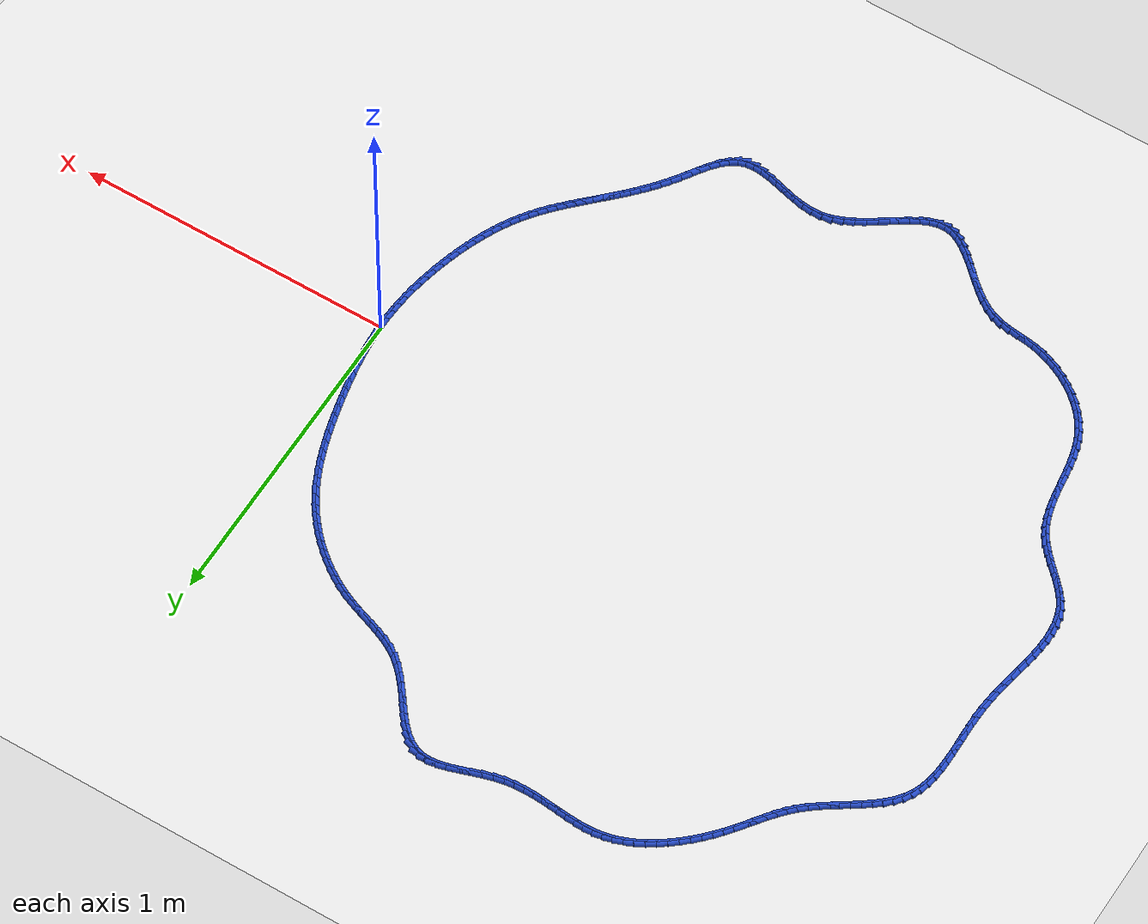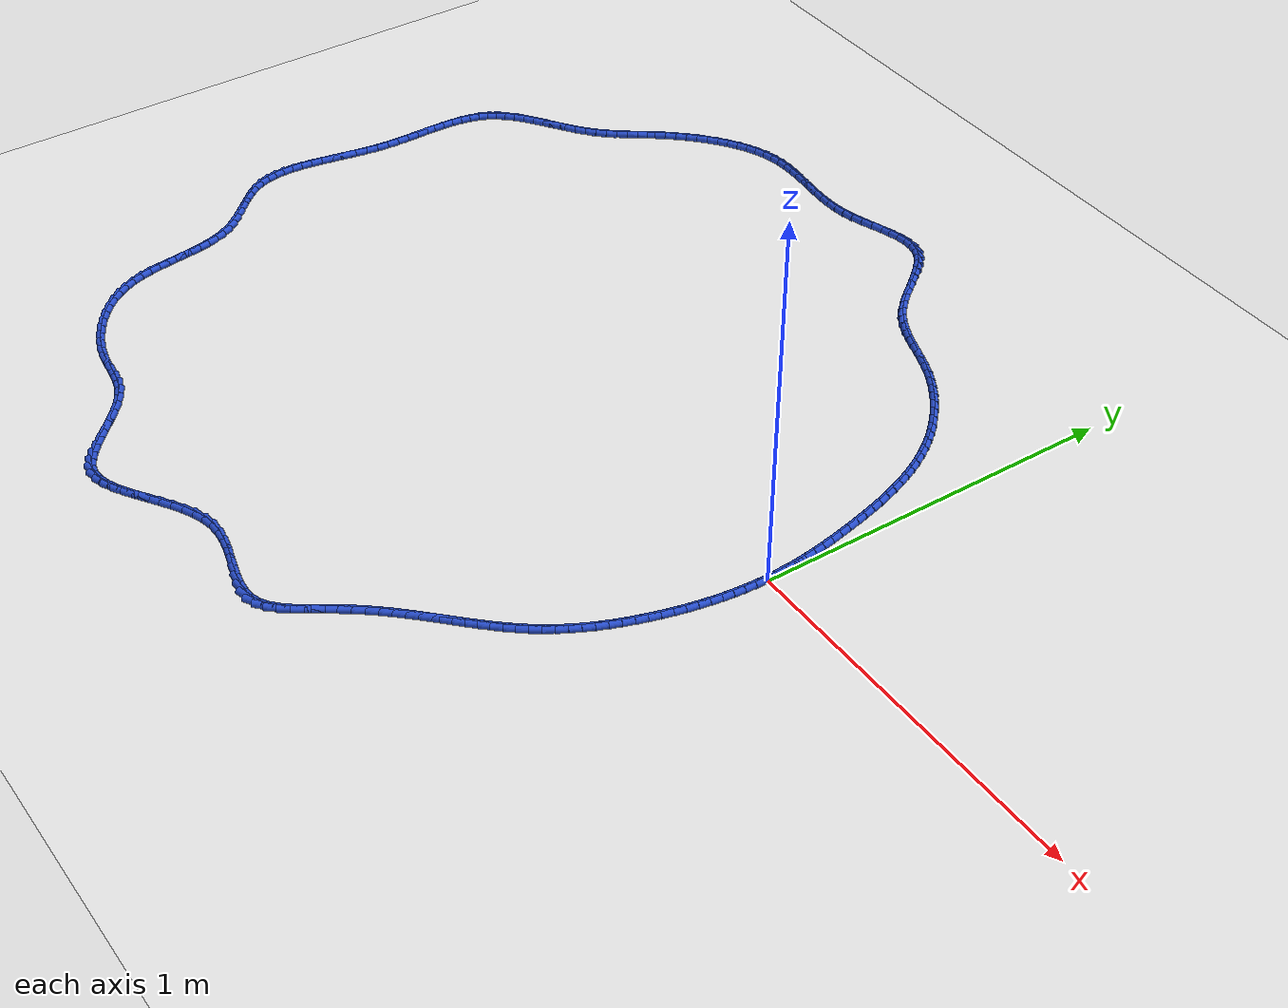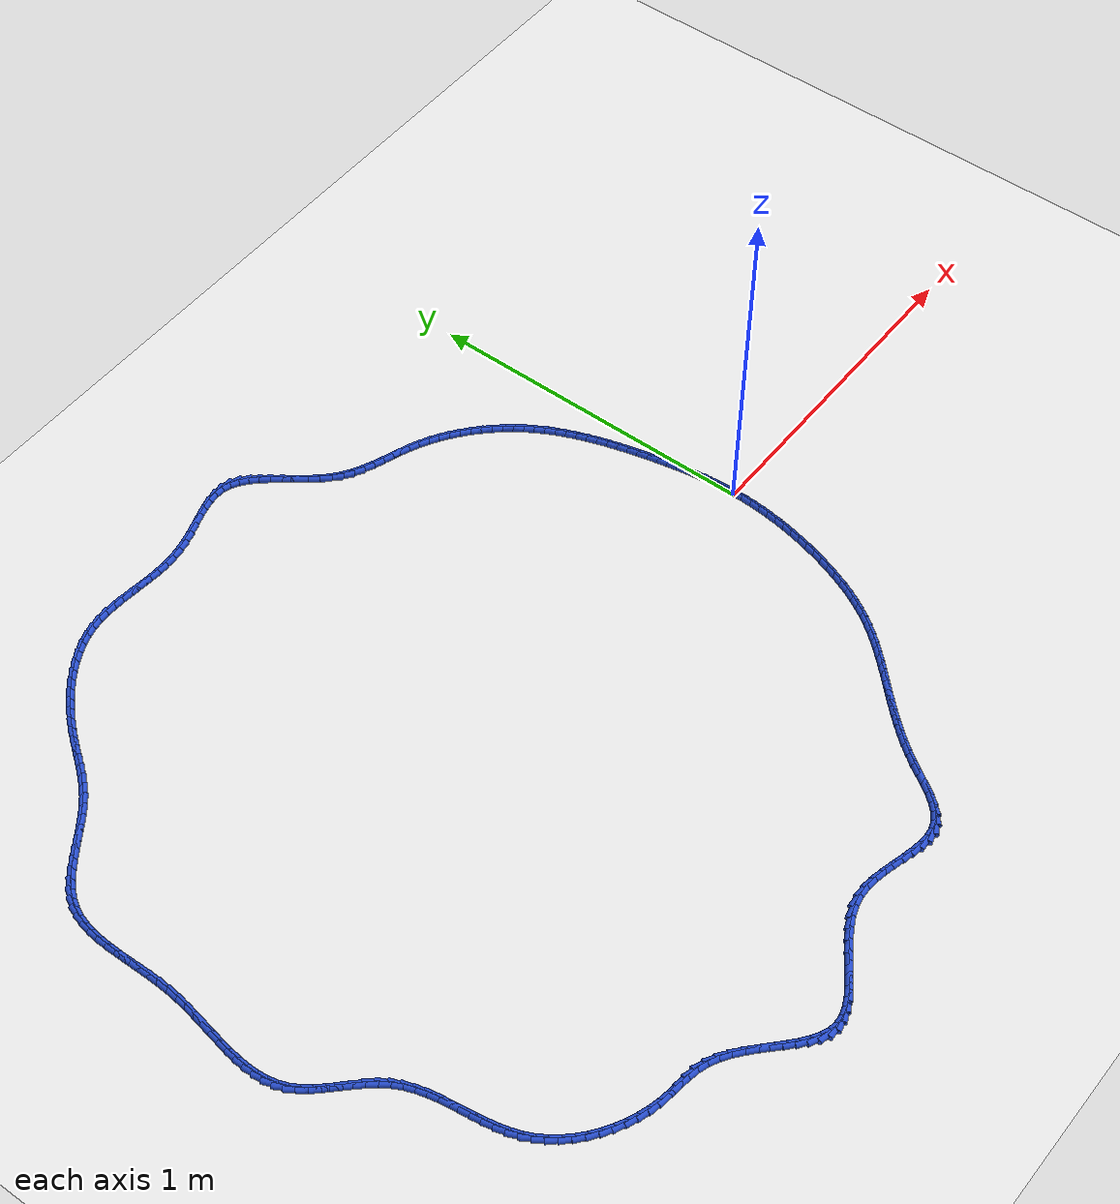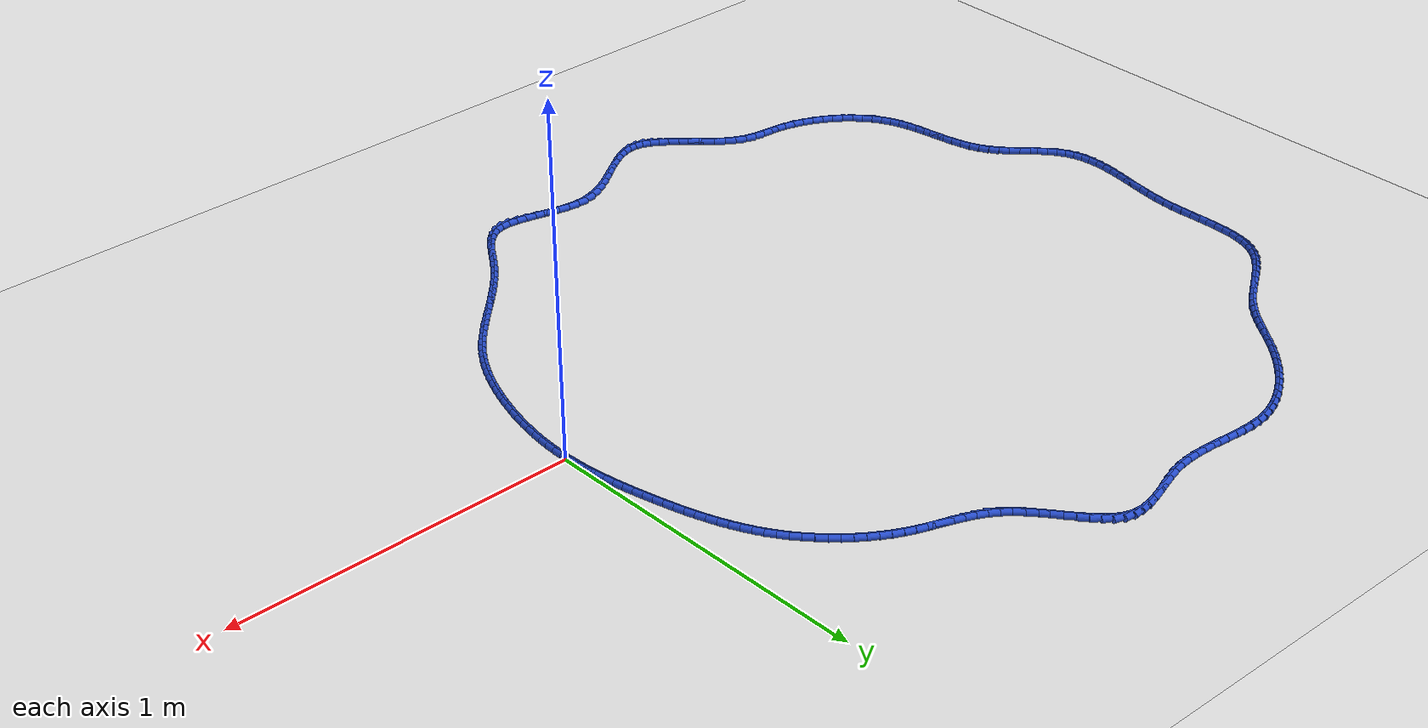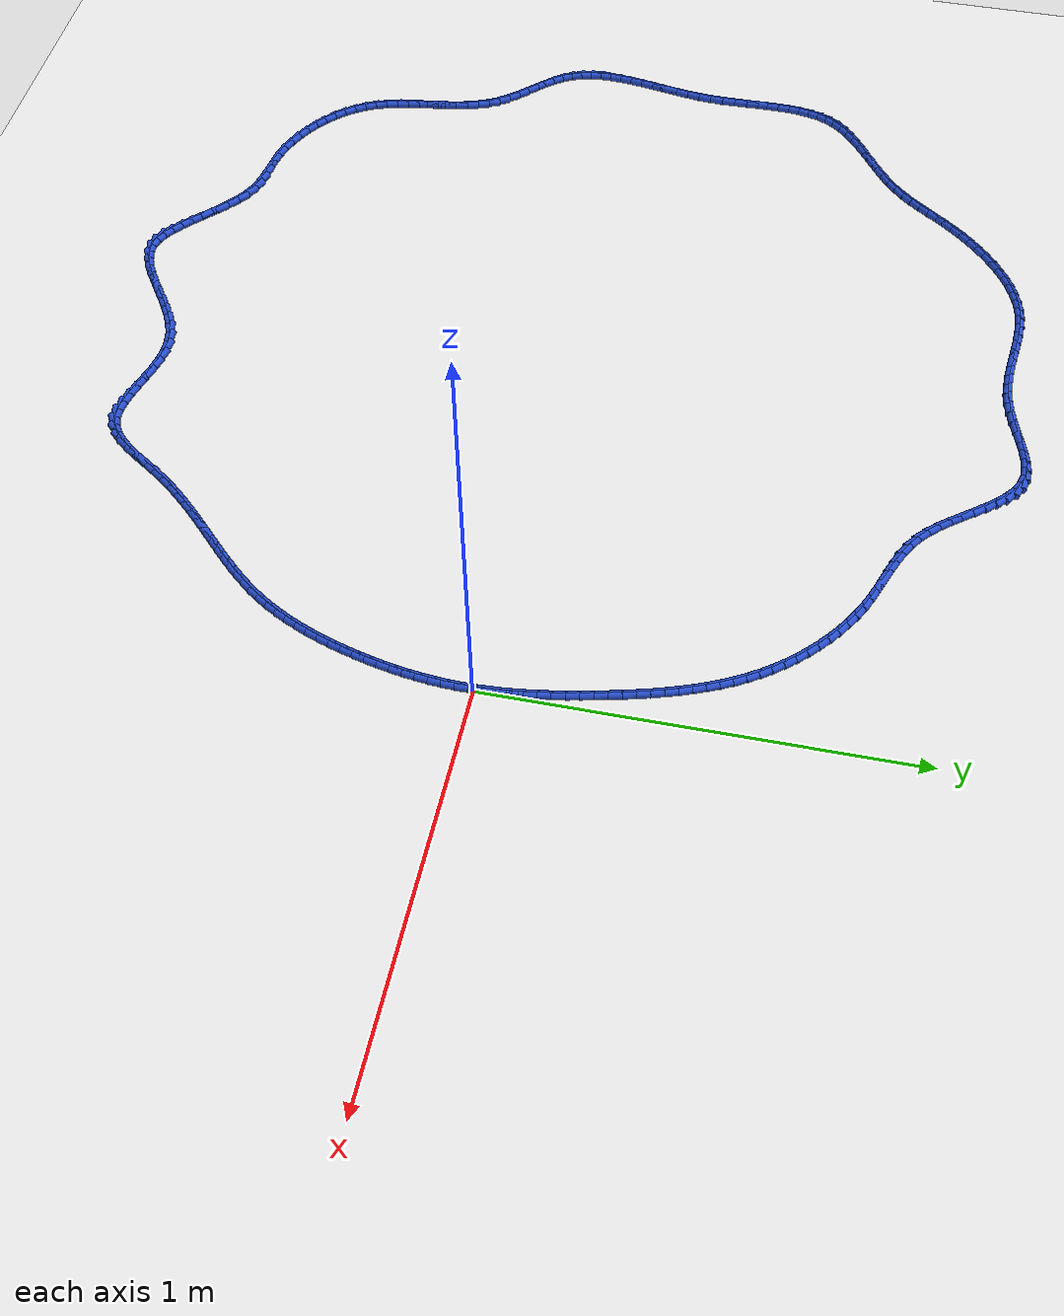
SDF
<sdf version="1.6">
 <world name="default">
  <light name="sun" type="directional">
   <pose>0 0 10 0 -0 0</pose>
   <diffuse>0.8 0.8 0.8 1</diffuse>
   <specular>0.2 0.2 0.2 1</specular>
   <attenuation>
    <range>1000</range>
    <constant>0.9</constant>
    <linear>0.01</linear>
    <quadratic>0.001</quadratic>
   </attenuation>
   <direction>-0.5 0.1 -0.9</direction>
  </light>
  <model name="ground_plane">
   <static>1</static>
   <link name="link">
    <collision name="collision">
     <geometry><plane><normal>0 0 1</normal><size>100 100</size></plane></geometry>
     <surface><friction><ode><mu>100</mu><mu2>50</mu2></ode></friction></surface>
    </collision>
    <visual name="visual">
     <cast_shadows>0</cast_shadows>
     <geometry><plane><normal>0 0 1</normal><size>100 100</size></plane></geometry>
     <material>
      <script><uri>file://media/materials/scripts/gazebo.material</uri><name>Gazebo/WhiteGlow</name></script>
     </material>
    </visual>
   </link>
  </model>
  <gravity>0 0 -9.8</gravity>
  <magnetic_field>6e-06 2.3e-05 -4.2e-05</magnetic_field>
  <atmosphere type="adiabatic"/>
  <physics name="default_physics" default="0" type="ode">
   <max_step_size>0.001</max_step_size>
   <real_time_factor>1</real_time_factor>
   <real_time_update_rate>1000</real_time_update_rate>
  </physics>
  <scene><ambient>0.4 0.4 0.4 1</ambient><background>0.7 0.7 0.7 1</background><shadows>1</shadows></scene>
  <spherical_coordinates>
   <surface_model>EARTH_WGS84</surface_model>
   <latitude_deg>0</latitude_deg>
   <longitude_deg>0</longitude_deg>
   <elevation>0</elevation>
   <heading_deg>0</heading_deg>
  </spherical_coordinates>
  <model name="line">
   <link name="link_0">
    <pose>-6.071532165918825e-18 4.85722573273506e-17 0.01 0 1.57 -1.5422927367857937</pose>
    <collision name="collision">
     <geometry><cylinder><radius>0.01</radius><length>0.08</length></cylinder></geometry>
    </collision>
    <visual name="visual">
     <material>
      <script><name>Gazebo/Blue</name><uri>file://media/materials/scripts/gazebo.material</uri></script>
     </material>
     <geometry><cylinder><radius>0.01</radius><length>0.08</length></cylinder></geometry>
    </visual>
   </link>
   <link name="link_1">
    <pose>-0.0008500700730344115 0.029815186291741774 0.01 0 1.57 -1.5089899252679961</pose>
    <collision name="collision">
     <geometry><cylinder><radius>0.01</radius><length>0.08</length></cylinder></geometry>
    </collision>
    <visual name="visual">
     <material>
      <script><name>Gazebo/Blue</name><uri>file://media/materials/scripts/gazebo.material</uri></script>
     </material>
     <geometry><cylinder><radius>0.01</radius><length>0.08</length></cylinder></geometry>
    </visual>
   </link>
   <link name="link_2">
    <pose>-0.0026938253464960774 0.05960832900175632 0.01 0 1.57 -1.4784900606739158</pose>
    <collision name="collision">
     <geometry><cylinder><radius>0.01</radius><length>0.08</length></cylinder></geometry>
    </collision>
    <visual name="visual">
     <material>
      <script><name>Gazebo/Blue</name><uri>file://media/materials/scripts/gazebo.material</uri></script>
     </material>
     <geometry><cylinder><radius>0.01</radius><length>0.08</length></cylinder></geometry>
    </visual>
   </link>
   <link name="link_3">
    <pose>-0.0054497243864304315 0.08937951943180696 0.01 0 1.57 -1.4508179641924235</pose>
    <collision name="collision">
     <geometry><cylinder><radius>0.01</radius><length>0.08</length></cylinder></geometry>
    </collision>
    <visual name="visual">
     <material>
      <script><name>Gazebo/Blue</name><uri>file://media/materials/scripts/gazebo.material</uri></script>
     </material>
     <geometry><cylinder><radius>0.01</radius><length>0.08</length></cylinder></geometry>
    </visual>
   </link>
   <link name="link_4">
    <pose>-0.009036225758882886 0.11912884888365684 0.01 0 1.57 -1.425974173129406</pose>
    <collision name="collision">
     <geometry><cylinder><radius>0.01</radius><length>0.08</length></cylinder></geometry>
    </collision>
    <visual name="visual">
     <material>
      <script><name>Gazebo/Blue</name><uri>file://media/materials/scripts/gazebo.material</uri></script>
     </material>
     <geometry><cylinder><radius>0.01</radius><length>0.08</length></cylinder></geometry>
    </visual>
   </link>
   <link name="link_5">
    <pose>-0.013371788029898852 0.1488564086590691 0.01 0 1.57 -1.403941627276447</pose>
    <collision name="collision">
     <geometry><cylinder><radius>0.01</radius><length>0.08</length></cylinder></geometry>
    </collision>
    <visual name="visual">
     <material>
      <script><name>Gazebo/Blue</name><uri>file://media/materials/scripts/gazebo.material</uri></script>
     </material>
     <geometry><cylinder><radius>0.01</radius><length>0.08</length></cylinder></geometry>
    </visual>
   </link>
   <link name="link_6">
    <pose>-0.018374869765523758 0.17856229005980703 0.01 0 1.57 -1.3846916934895022</pose>
    <collision name="collision">
     <geometry><cylinder><radius>0.01</radius><length>0.08</length></cylinder></geometry>
    </collision>
    <visual name="visual">
     <material>
      <script><name>Gazebo/Blue</name><uri>file://media/materials/scripts/gazebo.material</uri></script>
     </material>
     <geometry><cylinder><radius>0.01</radius><length>0.08</length></cylinder></geometry>
    </visual>
   </link>
   <link name="link_7">
    <pose>-0.02396392953180301 0.2082465843876337 0.01 0 1.57 -1.3681893877690723</pose>
    <collision name="collision">
     <geometry><cylinder><radius>0.01</radius><length>0.08</length></cylinder></geometry>
    </collision>
    <visual name="visual">
     <material>
      <script><name>Gazebo/Blue</name><uri>file://media/materials/scripts/gazebo.material</uri></script>
     </material>
     <geometry><cylinder><radius>0.01</radius><length>0.08</length></cylinder></geometry>
    </visual>
   </link>
   <link name="link_8">
    <pose>-0.030057425894782025 0.23790938294431227 0.01 0 1.57 -1.354397757085434</pose>
    <collision name="collision">
     <geometry><cylinder><radius>0.01</radius><length>0.08</length></cylinder></geometry>
    </collision>
    <visual name="visual">
     <material>
      <script><name>Gazebo/Blue</name><uri>file://media/materials/scripts/gazebo.material</uri></script>
     </material>
     <geometry><cylinder><radius>0.01</radius><length>0.08</length></cylinder></geometry>
    </visual>
   </link>
   <link name="link_9">
    <pose>-0.036573817420506236 0.2675507770316061 0.01 0 1.57 -1.3425047791238347</pose>
    <collision name="collision">
     <geometry><cylinder><radius>0.01</radius><length>0.08</length></cylinder></geometry>
    </collision>
    <visual name="visual">
     <material>
      <script><name>Gazebo/Blue</name><uri>file://media/materials/scripts/gazebo.material</uri></script>
     </material>
     <geometry><cylinder><radius>0.01</radius><length>0.08</length></cylinder></geometry>
    </visual>
   </link>
   <link name="link_10">
    <pose>-0.04345385833874382 0.29716247840001847 0.01 0 1.57 -1.3285737604182255</pose>
    <collision name="collision">
     <geometry><cylinder><radius>0.01</radius><length>0.08</length></cylinder></geometry>
    </collision>
    <visual name="visual">
     <material>
      <script><name>Gazebo/Blue</name><uri>file://media/materials/scripts/gazebo.material</uri></script>
     </material>
     <geometry><cylinder><radius>0.01</radius><length>0.08</length></cylinder></geometry>
    </visual>
   </link>
   <link name="link_11">
    <pose>-0.050750341684509856 0.32669409039173974 0.01 0 1.57 -1.3113362095584067</pose>
    <collision name="collision">
     <geometry><cylinder><radius>0.01</radius><length>0.08</length></cylinder></geometry>
    </collision>
    <visual name="visual">
     <material>
      <script><name>Gazebo/Blue</name><uri>file://media/materials/scripts/gazebo.material</uri></script>
     </material>
     <geometry><cylinder><radius>0.01</radius><length>0.08</length></cylinder></geometry>
    </visual>
   </link>
   <link name="link_12">
    <pose>-0.058551177147625755 0.35608201818573537 0.01 0 1.57 -1.2907302031593344</pose>
    <collision name="collision">
     <geometry><cylinder><radius>0.01</radius><length>0.08</length></cylinder></geometry>
    </collision>
    <visual name="visual">
     <material>
      <script><name>Gazebo/Blue</name><uri>file://media/materials/scripts/gazebo.material</uri></script>
     </material>
     <geometry><cylinder><radius>0.01</radius><length>0.08</length></cylinder></geometry>
    </visual>
   </link>
   <link name="link_13">
    <pose>-0.06694428671944992 0.38526266233758893 0.01 0 1.57 -1.2666827574717787</pose>
    <collision name="collision">
     <geometry><cylinder><radius>0.01</radius><length>0.08</length></cylinder></geometry>
    </collision>
    <visual name="visual">
     <material>
      <script><name>Gazebo/Blue</name><uri>file://media/materials/scripts/gazebo.material</uri></script>
     </material>
     <geometry><cylinder><radius>0.01</radius><length>0.08</length></cylinder></geometry>
    </visual>
   </link>
   <link name="link_14">
    <pose>-0.0760175923913409 0.4141724234028846 0.01 0 1.57 -1.2391159954920428</pose>
    <collision name="collision">
     <geometry><cylinder><radius>0.01</radius><length>0.08</length></cylinder></geometry>
    </collision>
    <visual name="visual">
     <material>
      <script><name>Gazebo/Blue</name><uri>file://media/materials/scripts/gazebo.material</uri></script>
     </material>
     <geometry><cylinder><radius>0.01</radius><length>0.08</length></cylinder></geometry>
    </visual>
   </link>
   <link name="link_15">
    <pose>-0.0858590161546571 0.4427477019372059 0.01 0 1.57 -1.2079554633256253</pose>
    <collision name="collision">
     <geometry><cylinder><radius>0.01</radius><length>0.08</length></cylinder></geometry>
    </collision>
    <visual name="visual">
     <material>
      <script><name>Gazebo/Blue</name><uri>file://media/materials/scripts/gazebo.material</uri></script>
     </material>
     <geometry><cylinder><radius>0.01</radius><length>0.08</length></cylinder></geometry>
    </visual>
   </link>
   <link name="link_16">
    <pose>-0.09655648000075702 0.47092489849613706 0.01 0 1.57 -1.1731404388087883</pose>
    <collision name="collision">
     <geometry><cylinder><radius>0.01</radius><length>0.08</length></cylinder></geometry>
    </collision>
    <visual name="visual">
     <material>
      <script><name>Gazebo/Blue</name><uri>file://media/materials/scripts/gazebo.material</uri></script>
     </material>
     <geometry><cylinder><radius>0.01</radius><length>0.08</length></cylinder></geometry>
    </visual>
   </link>
   <link name="link_17">
    <pose>-0.10819790592099916 0.49864041363526146 0.01 0 1.57 -1.1346363552337206</pose>
    <collision name="collision">
     <geometry><cylinder><radius>0.01</radius><length>0.08</length></cylinder></geometry>
    </collision>
    <visual name="visual">
     <material>
      <script><name>Gazebo/Blue</name><uri>file://media/materials/scripts/gazebo.material</uri></script>
     </material>
     <geometry><cylinder><radius>0.01</radius><length>0.08</length></cylinder></geometry>
    </visual>
   </link>
   <link name="link_18">
    <pose>-0.12087121590674191 0.5258306479101631 0.01 0 1.57 -1.0924491869391255</pose>
    <collision name="collision">
     <geometry><cylinder><radius>0.01</radius><length>0.08</length></cylinder></geometry>
    </collision>
    <visual name="visual">
     <material>
      <script><name>Gazebo/Blue</name><uri>file://media/materials/scripts/gazebo.material</uri></script>
     </material>
     <geometry><cylinder><radius>0.01</radius><length>0.08</length></cylinder></geometry>
    </visual>
   </link>
   <link name="link_19">
    <pose>-0.13466433194934374 0.5524320018764258 0.01 0 1.57 -1.0466412151511646</pose>
    <collision name="collision">
     <geometry><cylinder><radius>0.01</radius><length>0.08</length></cylinder></geometry>
    </collision>
    <visual name="visual">
     <material>
      <script><name>Gazebo/Blue</name><uri>file://media/materials/scripts/gazebo.material</uri></script>
     </material>
     <geometry><cylinder><radius>0.01</radius><length>0.08</length></cylinder></geometry>
    </visual>
   </link>
   <link name="link_20">
    <pose>-0.1496651760401632 0.5783808760896336 0.01 0 1.57 -0.9973470188442682</pose>
    <collision name="collision">
     <geometry><cylinder><radius>0.01</radius><length>0.08</length></cylinder></geometry>
    </collision>
    <visual name="visual">
     <material>
      <script><name>Gazebo/Blue</name><uri>file://media/materials/scripts/gazebo.material</uri></script>
     </material>
     <geometry><cylinder><radius>0.01</radius><length>0.08</length></cylinder></geometry>
    </visual>
   </link>
   <link name="link_21">
    <pose>-0.16596167017055868 0.6036136711053701 0.01 0 1.57 -0.9453736026981899</pose>
    <collision name="collision">
     <geometry><cylinder><radius>0.01</radius><length>0.08</length></cylinder></geometry>
    </collision>
    <visual name="visual">
     <material>
      <script><name>Gazebo/Blue</name><uri>file://media/materials/scripts/gazebo.material</uri></script>
     </material>
     <geometry><cylinder><radius>0.01</radius><length>0.08</length></cylinder></geometry>
    </visual>
   </link>
   <link name="link_22">
    <pose>-0.18361828702493266 0.628064504447458 0.01 0 1.57 -0.8934376284578187</pose>
    <collision name="collision">
     <geometry><cylinder><radius>0.01</radius><length>0.08</length></cylinder></geometry>
    </collision>
    <visual name="visual">
     <material>
      <script><name>Gazebo/Blue</name><uri>file://media/materials/scripts/gazebo.material</uri></script>
     </material>
     <geometry><cylinder><radius>0.01</radius><length>0.08</length></cylinder></geometry>
    </visual>
   </link>
   <link name="link_23">
    <pose>-0.20259395701942093 0.6516572180119145 0.01 0 1.57 -0.8420445888615028</pose>
    <collision name="collision">
     <geometry><cylinder><radius>0.01</radius><length>0.08</length></cylinder></geometry>
    </collision>
    <visual name="visual">
     <material>
      <script><name>Gazebo/Blue</name><uri>file://media/materials/scripts/gazebo.material</uri></script>
     </material>
     <geometry><cylinder><radius>0.01</radius><length>0.08</length></cylinder></geometry>
    </visual>
   </link>
   <link name="link_24">
    <pose>-0.22281793014236864 0.6743127639991473 0.01 0 1.57 -0.7909232255327905</pose>
    <collision name="collision">
     <geometry><cylinder><radius>0.01</radius><length>0.08</length></cylinder></geometry>
    </collision>
    <visual name="visual">
     <material>
      <script><name>Gazebo/Blue</name><uri>file://media/materials/scripts/gazebo.material</uri></script>
     </material>
     <geometry><cylinder><radius>0.01</radius><length>0.08</length></cylinder></geometry>
    </visual>
   </link>
   <link name="link_25">
    <pose>-0.24421945477810603 0.6959520944533982 0.01 0 1.57 -0.7398049628768644</pose>
    <collision name="collision">
     <geometry><cylinder><radius>0.01</radius><length>0.08</length></cylinder></geometry>
    </collision>
    <visual name="visual">
     <material>
      <script><name>Gazebo/Blue</name><uri>file://media/materials/scripts/gazebo.material</uri></script>
     </material>
     <geometry><cylinder><radius>0.01</radius><length>0.08</length></cylinder></geometry>
    </visual>
   </link>
   <link name="link_26">
    <pose>-0.26672777931096314 0.7164961614189078 0.01 0 1.57 -0.688424894510176</pose>
    <collision name="collision">
     <geometry><cylinder><radius>0.01</radius><length>0.08</length></cylinder></geometry>
    </collision>
    <visual name="visual">
     <material>
      <script><name>Gazebo/Blue</name><uri>file://media/materials/scripts/gazebo.material</uri></script>
     </material>
     <geometry><cylinder><radius>0.01</radius><length>0.08</length></cylinder></geometry>
    </visual>
   </link>
   <link name="link_27">
    <pose>-0.2902721521252701 0.7358659169399174 0.01 0 1.57 -0.6365228189762627</pose>
    <collision name="collision">
     <geometry><cylinder><radius>0.01</radius><length>0.08</length></cylinder></geometry>
    </collision>
    <visual name="visual">
     <material>
      <script><name>Gazebo/Blue</name><uri>file://media/materials/scripts/gazebo.material</uri></script>
     </material>
     <geometry><cylinder><radius>0.01</radius><length>0.08</length></cylinder></geometry>
    </visual>
   </link>
   <link name="link_28">
    <pose>-0.3147818216053569 0.7539823130606679 0.01 0 1.57 -0.5838446735683452</pose>
    <collision name="collision">
     <geometry><cylinder><radius>0.01</radius><length>0.08</length></cylinder></geometry>
    </collision>
    <visual name="visual">
     <material>
      <script><name>Gazebo/Blue</name><uri>file://media/materials/scripts/gazebo.material</uri></script>
     </material>
     <geometry><cylinder><radius>0.01</radius><length>0.08</length></cylinder></geometry>
    </visual>
   </link>
   <link name="link_29">
    <pose>-0.3401860361355535 0.7707663018254001 0.01 0 1.57 -0.5301446679307832</pose>
    <collision name="collision">
     <geometry><cylinder><radius>0.01</radius><length>0.08</length></cylinder></geometry>
    </collision>
    <visual name="visual">
     <material>
      <script><name>Gazebo/Blue</name><uri>file://media/materials/scripts/gazebo.material</uri></script>
     </material>
     <geometry><cylinder><radius>0.01</radius><length>0.08</length></cylinder></geometry>
    </visual>
   </link>
   <link name="link_30">
    <pose>-0.36641404410019035 0.7861388352783555 0.01 0 1.57 -0.47518841329558575</pose>
    <collision name="collision">
     <geometry><cylinder><radius>0.01</radius><length>0.08</length></cylinder></geometry>
    </collision>
    <visual name="visual">
     <material>
      <script><name>Gazebo/Blue</name><uri>file://media/materials/scripts/gazebo.material</uri></script>
     </material>
     <geometry><cylinder><radius>0.01</radius><length>0.08</length></cylinder></geometry>
    </visual>
   </link>
   <link name="link_31">
    <pose>-0.3933950938835974 0.8000208654637748 0.01 0 1.57 -0.4190884374159416</pose>
    <collision name="collision">
     <geometry><cylinder><radius>0.01</radius><length>0.08</length></cylinder></geometry>
    </collision>
    <visual name="visual">
     <material>
      <script><name>Gazebo/Blue</name><uri>file://media/materials/scripts/gazebo.material</uri></script>
     </material>
     <geometry><cylinder><radius>0.01</radius><length>0.08</length></cylinder></geometry>
    </visual>
   </link>
   <link name="link_32">
    <pose>-0.42105552526885476 0.8123430244261538 0.01 0 1.57 -0.3726044671047308</pose>
    <collision name="collision">
     <geometry><cylinder><radius>0.01</radius><length>0.08</length></cylinder></geometry>
    </collision>
    <visual name="visual">
     <material>
      <script><name>Gazebo/Blue</name><uri>file://media/materials/scripts/gazebo.material</uri></script>
     </material>
     <geometry><cylinder><radius>0.01</radius><length>0.08</length></cylinder></geometry>
    </visual>
   </link>
   <link name="link_33">
    <pose>-0.44922615073374855 0.8233538648392147 0.01 0 1.57 -0.3488961124381519</pose>
    <collision name="collision">
     <geometry><cylinder><radius>0.01</radius><length>0.08</length></cylinder></geometry>
    </collision>
    <visual name="visual">
     <material>
      <script><name>Gazebo/Blue</name><uri>file://media/materials/scripts/gazebo.material</uri></script>
     </material>
     <geometry><cylinder><radius>0.01</radius><length>0.08</length></cylinder></geometry>
    </visual>
   </link>
   <link name="link_34">
    <pose>-0.4776229807150205 0.833684007488129 0.01 0 1.57 -0.348773443359095</pose>
    <collision name="collision">
     <geometry><cylinder><radius>0.01</radius><length>0.08</length></cylinder></geometry>
    </collision>
    <visual name="visual">
     <material>
      <script><name>Gazebo/Blue</name><uri>file://media/materials/scripts/gazebo.material</uri></script>
     </material>
     <geometry><cylinder><radius>0.01</radius><length>0.08</length></cylinder></geometry>
    </visual>
   </link>
   <link name="link_35">
    <pose>-0.5059552212323084 0.8439867186682762 0.01 0 1.57 -0.3724011202834807</pose>
    <collision name="collision">
     <geometry><cylinder><radius>0.01</radius><length>0.08</length></cylinder></geometry>
    </collision>
    <visual name="visual">
     <material>
      <script><name>Gazebo/Blue</name><uri>file://media/materials/scripts/gazebo.material</uri></script>
     </material>
     <geometry><cylinder><radius>0.01</radius><length>0.08</length></cylinder></geometry>
    </visual>
   </link>
   <link name="link_36">
    <pose>-0.5339320783052496 0.8549152646750361 0.01 0 1.57 -0.42007674654019456</pose>
    <collision name="collision">
     <geometry><cylinder><radius>0.01</radius><length>0.08</length></cylinder></geometry>
    </collision>
    <visual name="visual">
     <material>
      <script><name>Gazebo/Blue</name><uri>file://media/materials/scripts/gazebo.material</uri></script>
     </material>
     <geometry><cylinder><radius>0.01</radius><length>0.08</length></cylinder></geometry>
    </visual>
   </link>
   <link name="link_37">
    <pose>-0.5612627579534817 0.8671229118037881 0.01 0 1.57 -0.49182471932828387</pose>
    <collision name="collision">
     <geometry><cylinder><radius>0.01</radius><length>0.08</length></cylinder></geometry>
    </collision>
    <visual name="visual">
     <material>
      <script><name>Gazebo/Blue</name><uri>file://media/materials/scripts/gazebo.material</uri></script>
     </material>
     <geometry><cylinder><radius>0.01</radius><length>0.08</length></cylinder></geometry>
    </visual>
   </link>
   <link name="link_38">
    <pose>-0.5876564661966422 0.8812629263499128 0.01 0 1.57 -0.5865804642303438</pose>
    <collision name="collision">
     <geometry><cylinder><radius>0.01</radius><length>0.08</length></cylinder></geometry>
    </collision>
    <visual name="visual">
     <material>
      <script><name>Gazebo/Blue</name><uri>file://media/materials/scripts/gazebo.material</uri></script>
     </material>
     <geometry><cylinder><radius>0.01</radius><length>0.08</length></cylinder></geometry>
    </visual>
   </link>
   <link name="link_39">
    <pose>-0.6128224090543692 0.8979885746087894 0.01 0 1.57 -0.6993807031024076</pose>
    <collision name="collision">
     <geometry><cylinder><radius>0.01</radius><length>0.08</length></cylinder></geometry>
    </collision>
    <visual name="visual">
     <material>
      <script><name>Gazebo/Blue</name><uri>file://media/materials/scripts/gazebo.material</uri></script>
     </material>
     <geometry><cylinder><radius>0.01</radius><length>0.08</length></cylinder></geometry>
    </visual>
   </link>
   <link name="link_40">
    <pose>-0.6364909742992195 0.917899288267042 0.01 0 1.57 -0.7989283197847066</pose>
    <collision name="collision">
     <geometry><cylinder><radius>0.01</radius><length>0.08</length></cylinder></geometry>
    </collision>
    <visual name="visual">
     <material>
      <script><name>Gazebo/Blue</name><uri>file://media/materials/scripts/gazebo.material</uri></script>
     </material>
     <geometry><cylinder><radius>0.01</radius><length>0.08</length></cylinder></geometry>
    </visual>
   </link>
   <link name="link_41">
    <pose>-0.6587267636403098 0.9407450756144885 0.01 0 1.57 -0.8661080932153845</pose>
    <collision name="collision">
     <geometry><cylinder><radius>0.01</radius><length>0.08</length></cylinder></geometry>
    </collision>
    <visual name="visual">
     <material>
      <script><name>Gazebo/Blue</name><uri>file://media/materials/scripts/gazebo.material</uri></script>
     </material>
     <geometry><cylinder><radius>0.01</radius><length>0.08</length></cylinder></geometry>
    </visual>
   </link>
   <link name="link_42">
    <pose>-0.6798607875677312 0.9655988521362451 0.01 0 1.57 -0.9046314336954666</pose>
    <collision name="collision">
     <geometry><cylinder><radius>0.01</radius><length>0.08</length></cylinder></geometry>
    </collision>
    <visual name="visual">
     <material>
      <script><name>Gazebo/Blue</name><uri>file://media/materials/scripts/gazebo.material</uri></script>
     </material>
     <geometry><cylinder><radius>0.01</radius><length>0.08</length></cylinder></geometry>
    </visual>
   </link>
   <link name="link_43">
    <pose>-0.7002314583482774 0.9915147212883009 0.01 0 1.57 -0.917008511958578</pose>
    <collision name="collision">
     <geometry><cylinder><radius>0.01</radius><length>0.08</length></cylinder></geometry>
    </collision>
    <visual name="visual">
     <material>
      <script><name>Gazebo/Blue</name><uri>file://media/materials/scripts/gazebo.material</uri></script>
     </material>
     <geometry><cylinder><radius>0.01</radius><length>0.08</length></cylinder></geometry>
    </visual>
   </link>
   <link name="link_44">
    <pose>-0.7201771882487424 1.017546786526646 0.01 0 1.57 -0.9034218260897235</pose>
    <collision name="collision">
     <geometry><cylinder><radius>0.01</radius><length>0.08</length></cylinder></geometry>
    </collision>
    <visual name="visual">
     <material>
      <script><name>Gazebo/Blue</name><uri>file://media/materials/scripts/gazebo.material</uri></script>
     </material>
     <geometry><cylinder><radius>0.01</radius><length>0.08</length></cylinder></geometry>
    </visual>
   </link>
   <link name="link_45">
    <pose>-0.7400363895359203 1.0427491513072698 0.01 0 1.57 -0.8614077679691307</pose>
    <collision name="collision">
     <geometry><cylinder><radius>0.01</radius><length>0.08</length></cylinder></geometry>
    </collision>
    <visual name="visual">
     <material>
      <script><name>Gazebo/Blue</name><uri>file://media/materials/scripts/gazebo.material</uri></script>
     </material>
     <geometry><cylinder><radius>0.01</radius><length>0.08</length></cylinder></geometry>
    </visual>
   </link>
   <link name="link_46">
    <pose>-0.760147474476605 1.0661759190861624 0.01 0 1.57 -0.7854921910880401</pose>
    <collision name="collision">
     <geometry><cylinder><radius>0.01</radius><length>0.08</length></cylinder></geometry>
    </collision>
    <visual name="visual">
     <material>
      <script><name>Gazebo/Blue</name><uri>file://media/materials/scripts/gazebo.material</uri></script>
     </material>
     <geometry><cylinder><radius>0.01</radius><length>0.08</length></cylinder></geometry>
    </visual>
   </link>
   <link name="link_47">
    <pose>-0.7808488553375901 1.0868811933193125 0.01 0 1.57 -0.6671919051729979</pose>
    <collision name="collision">
     <geometry><cylinder><radius>0.01</radius><length>0.08</length></cylinder></geometry>
    </collision>
    <visual name="visual">
     <material>
      <script><name>Gazebo/Blue</name><uri>file://media/materials/scripts/gazebo.material</uri></script>
     </material>
     <geometry><cylinder><radius>0.01</radius><length>0.08</length></cylinder></geometry>
    </visual>
   </link>
   <link name="link_48">
    <pose>-0.8024789443856698 1.1039190774627106 0.01 0 1.57 -0.4971633687467852</pose>
    <collision name="collision">
     <geometry><cylinder><radius>0.01</radius><length>0.08</length></cylinder></geometry>
    </collision>
    <visual name="visual">
     <material>
      <script><name>Gazebo/Blue</name><uri>file://media/materials/scripts/gazebo.material</uri></script>
     </material>
     <geometry><cylinder><radius>0.01</radius><length>0.08</length></cylinder></geometry>
    </visual>
   </link>
   <link name="link_49">
    <pose>-0.8253761538876374 1.1163436749723457 0.01 0 1.57 -0.27399471094471256</pose>
    <collision name="collision">
     <geometry><cylinder><radius>0.01</radius><length>0.08</length></cylinder></geometry>
    </collision>
    <visual name="visual">
     <material>
      <script><name>Gazebo/Blue</name><uri>file://media/materials/scripts/gazebo.material</uri></script>
     </material>
     <geometry><cylinder><radius>0.01</radius><length>0.08</length></cylinder></geometry>
    </visual>
   </link>
   <link name="link_50">
    <pose>-0.8498733428551785 1.1232289432125269 0.01 0 1.57 -0.04825395189657477</pose>
    <collision name="collision">
     <geometry><cylinder><radius>0.01</radius><length>0.08</length></cylinder></geometry>
    </collision>
    <visual name="visual">
     <material>
      <script><name>Gazebo/Blue</name><uri>file://media/materials/scripts/gazebo.material</uri></script>
     </material>
     <geometry><cylinder><radius>0.01</radius><length>0.08</length></cylinder></geometry>
    </visual>
   </link>
   <link name="link_51">
    <pose>-0.8760670094472489 1.1244938730654117 0.01 0 1.57 0.1185126245627761</pose>
    <collision name="collision">
     <geometry><cylinder><radius>0.01</radius><length>0.08</length></cylinder></geometry>
    </collision>
    <visual name="visual">
     <material>
      <script><name>Gazebo/Blue</name><uri>file://media/materials/scripts/gazebo.material</uri></script>
     </material>
     <geometry><cylinder><radius>0.01</radius><length>0.08</length></cylinder></geometry>
    </visual>
   </link>
   <link name="link_52">
    <pose>-0.9037342088258361 1.1211995228763845 0.01 0 1.57 0.2282279077582263</pose>
    <collision name="collision">
     <geometry><cylinder><radius>0.01</radius><length>0.08</length></cylinder></geometry>
    </collision>
    <visual name="visual">
     <material>
      <script><name>Gazebo/Blue</name><uri>file://media/materials/scripts/gazebo.material</uri></script>
     </material>
     <geometry><cylinder><radius>0.01</radius><length>0.08</length></cylinder></geometry>
    </visual>
   </link>
   <link name="link_53">
    <pose>-0.9326293524129078 1.1144879065258284 0.01 0 1.57 0.2921818875425154</pose>
    <collision name="collision">
     <geometry><cylinder><radius>0.01</radius><length>0.08</length></cylinder></geometry>
    </collision>
    <visual name="visual">
     <material>
      <script><name>Gazebo/Blue</name><uri>file://media/materials/scripts/gazebo.material</uri></script>
     </material>
     <geometry><cylinder><radius>0.01</radius><length>0.08</length></cylinder></geometry>
    </visual>
   </link>
   <link name="link_54">
    <pose>-0.9625068516304323 1.1055010378941248 0.01 0 1.57 0.31925999525281823</pose>
    <collision name="collision">
     <geometry><cylinder><radius>0.01</radius><length>0.08</length></cylinder></geometry>
    </collision>
    <visual name="visual">
     <material>
      <script><name>Gazebo/Blue</name><uri>file://media/materials/scripts/gazebo.material</uri></script>
     </material>
     <geometry><cylinder><radius>0.01</radius><length>0.08</length></cylinder></geometry>
    </visual>
   </link>
   <link name="link_55">
    <pose>-0.9931211179003775 1.0953809308616567 0.01 0 1.57 0.3142918558554758</pose>
    <collision name="collision">
     <geometry><cylinder><radius>0.01</radius><length>0.08</length></cylinder></geometry>
    </collision>
    <visual name="visual">
     <material>
      <script><name>Gazebo/Blue</name><uri>file://media/materials/scripts/gazebo.material</uri></script>
     </material>
     <geometry><cylinder><radius>0.01</radius><length>0.08</length></cylinder></geometry>
    </visual>
   </link>
   <link name="link_56">
    <pose>-1.0242265626447122 1.0852695993088064 0.01 0 1.57 0.2783911840773198</pose>
    <collision name="collision">
     <geometry><cylinder><radius>0.01</radius><length>0.08</length></cylinder></geometry>
    </collision>
    <visual name="visual">
     <material>
      <script><name>Gazebo/Blue</name><uri>file://media/materials/scripts/gazebo.material</uri></script>
     </material>
     <geometry><cylinder><radius>0.01</radius><length>0.08</length></cylinder></geometry>
    </visual>
   </link>
   <link name="link_57">
    <pose>-1.055577597285404 1.0763090571159561 0.01 0 1.57 0.2096859835090827</pose>
    <collision name="collision">
     <geometry><cylinder><radius>0.01</radius><length>0.08</length></cylinder></geometry>
    </collision>
    <visual name="visual">
     <material>
      <script><name>Gazebo/Blue</name><uri>file://media/materials/scripts/gazebo.material</uri></script>
     </material>
     <geometry><cylinder><radius>0.01</radius><length>0.08</length></cylinder></geometry>
    </visual>
   </link>
   <link name="link_58">
    <pose>-1.0869292205018035 1.069636986998565 0.01 0 1.57 0.12062834429621352</pose>
    <collision name="collision">
     <geometry><cylinder><radius>0.01</radius><length>0.08</length></cylinder></geometry>
    </collision>
    <visual name="visual">
     <material>
      <script><name>Gazebo/Blue</name><uri>file://media/materials/scripts/gazebo.material</uri></script>
     </material>
     <geometry><cylinder><radius>0.01</radius><length>0.08</length></cylinder></geometry>
    </visual>
   </link>
   <link name="link_59">
    <pose>-1.1181087774655243 1.0658574988317433 0.01 0 1.57 0.04272394404241163</pose>
    <collision name="collision">
     <geometry><cylinder><radius>0.01</radius><length>0.08</length></cylinder></geometry>
    </collision>
    <visual name="visual">
     <material>
      <script><name>Gazebo/Blue</name><uri>file://media/materials/scripts/gazebo.material</uri></script>
     </material>
     <geometry><cylinder><radius>0.01</radius><length>0.08</length></cylinder></geometry>
    </visual>
   </link>
   <link name="link_60">
    <pose>-1.1490848193245344 1.0645332743366924 0.01 0 1.57 -0.01863873819086451</pose>
    <collision name="collision">
     <geometry><cylinder><radius>0.01</radius><length>0.08</length></cylinder></geometry>
    </collision>
    <visual name="visual">
     <material>
      <script><name>Gazebo/Blue</name><uri>file://media/materials/scripts/gazebo.material</uri></script>
     </material>
     <geometry><cylinder><radius>0.01</radius><length>0.08</length></cylinder></geometry>
    </visual>
   </link>
   <link name="link_61">
    <pose>-1.1798422187790223 1.065106619847994 0.01 0 1.57 -0.06259813172790533</pose>
    <collision name="collision">
     <geometry><cylinder><radius>0.01</radius><length>0.08</length></cylinder></geometry>
    </collision>
    <visual name="visual">
     <material>
      <script><name>Gazebo/Blue</name><uri>file://media/materials/scripts/gazebo.material</uri></script>
     </material>
     <geometry><cylinder><radius>0.01</radius><length>0.08</length></cylinder></geometry>
    </visual>
   </link>
   <link name="link_62">
    <pose>-1.2103658485291757 1.0670198417002306 0.01 0 1.57 -0.08879736206167604</pose>
    <collision name="collision">
     <geometry><cylinder><radius>0.01</radius><length>0.08</length></cylinder></geometry>
    </collision>
    <visual name="visual">
     <material>
      <script><name>Gazebo/Blue</name><uri>file://media/materials/scripts/gazebo.material</uri></script>
     </material>
     <geometry><cylinder><radius>0.01</radius><length>0.08</length></cylinder></geometry>
    </visual>
   </link>
   <link name="link_63">
    <pose>-1.2406405812751828 1.0697152462279833 0.01 0 1.57 -0.0969897783950628</pose>
    <collision name="collision">
     <geometry><cylinder><radius>0.01</radius><length>0.08</length></cylinder></geometry>
    </collision>
    <visual name="visual">
     <material>
      <script><name>Gazebo/Blue</name><uri>file://media/materials/scripts/gazebo.material</uri></script>
     </material>
     <geometry><cylinder><radius>0.01</radius><length>0.08</length></cylinder></geometry>
    </visual>
   </link>
   <link name="link_64">
    <pose>-1.270651289717232 1.072635139765835 0.01 0 1.57 -0.08678294050183206</pose>
    <collision name="collision">
     <geometry><cylinder><radius>0.01</radius><length>0.08</length></cylinder></geometry>
    </collision>
    <visual name="visual">
     <material>
      <script><name>Gazebo/Blue</name><uri>file://media/materials/scripts/gazebo.material</uri></script>
     </material>
     <geometry><cylinder><radius>0.01</radius><length>0.08</length></cylinder></geometry>
    </visual>
   </link>
   <link name="link_65">
    <pose>-1.300382846555511 1.075221828648367 0.01 0 1.57 -0.05754331067035591</pose>
    <collision name="collision">
     <geometry><cylinder><radius>0.01</radius><length>0.08</length></cylinder></geometry>
    </collision>
    <visual name="visual">
     <material>
      <script><name>Gazebo/Blue</name><uri>file://media/materials/scripts/gazebo.material</uri></script>
     </material>
     <geometry><cylinder><radius>0.01</radius><length>0.08</length></cylinder></geometry>
    </visual>
   </link>
   <link name="link_66">
    <pose>-1.3298201244902086 1.0769176192101617 0.01 0 1.57 -0.008486464217886838</pose>
    <collision name="collision">
     <geometry><cylinder><radius>0.01</radius><length>0.08</length></cylinder></geometry>
    </collision>
    <visual name="visual">
     <material>
      <script><name>Gazebo/Blue</name><uri>file://media/materials/scripts/gazebo.material</uri></script>
     </material>
     <geometry><cylinder><radius>0.01</radius><length>0.08</length></cylinder></geometry>
    </visual>
   </link>
   <link name="link_67">
    <pose>-1.3589479962215116 1.077164817785801 0.01 0 1.57 0.0609965730885073</pose>
    <collision name="collision">
     <geometry><cylinder><radius>0.01</radius><length>0.08</length></cylinder></geometry>
    </collision>
    <visual name="visual">
     <material>
      <script><name>Gazebo/Blue</name><uri>file://media/materials/scripts/gazebo.material</uri></script>
     </material>
     <geometry><cylinder><radius>0.01</radius><length>0.08</length></cylinder></geometry>
    </visual>
   </link>
   <link name="link_68">
    <pose>-1.3877513344496097 1.0754057307098672 0.01 0 1.57 0.15063431623236334</pose>
    <collision name="collision">
     <geometry><cylinder><radius>0.01</radius><length>0.08</length></cylinder></geometry>
    </collision>
    <visual name="visual">
     <material>
      <script><name>Gazebo/Blue</name><uri>file://media/materials/scripts/gazebo.material</uri></script>
     </material>
     <geometry><cylinder><radius>0.01</radius><length>0.08</length></cylinder></geometry>
    </visual>
   </link>
   <link name="link_69">
    <pose>-1.416214802204849 1.071085429285288 0.01 0 1.57 0.2501114201915283</pose>
    <collision name="collision">
     <geometry><cylinder><radius>0.01</radius><length>0.08</length></cylinder></geometry>
    </collision>
    <visual name="visual">
     <material>
      <script><name>Gazebo/Blue</name><uri>file://media/materials/scripts/gazebo.material</uri></script>
     </material>
     <geometry><cylinder><radius>0.01</radius><length>0.08</length></cylinder></geometry>
    </visual>
   </link>
   <link name="link_70">
    <pose>-1.4443032747542166 1.0639099309726727 0.01 0 1.57 0.34241282268030326</pose>
    <collision name="collision">
     <geometry><cylinder><radius>0.01</radius><length>0.08</length></cylinder></geometry>
    </collision>
    <visual name="visual">
     <material>
      <script><name>Gazebo/Blue</name><uri>file://media/materials/scripts/gazebo.material</uri></script>
     </material>
     <geometry><cylinder><radius>0.01</radius><length>0.08</length></cylinder></geometry>
    </visual>
   </link>
   <link name="link_71">
    <pose>-1.4719458836809427 1.0540566140816165 0.01 0 1.57 0.4258939403074208</pose>
    <collision name="collision">
     <geometry><cylinder><radius>0.01</radius><length>0.08</length></cylinder></geometry>
    </collision>
    <visual name="visual">
     <material>
      <script><name>Gazebo/Blue</name><uri>file://media/materials/scripts/gazebo.material</uri></script>
     </material>
     <geometry><cylinder><radius>0.01</radius><length>0.08</length></cylinder></geometry>
    </visual>
   </link>
   <link name="link_72">
    <pose>-1.499068005570366 1.0417523750130102 0.01 0 1.57 0.5010588615956438</pose>
    <collision name="collision">
     <geometry><cylinder><radius>0.01</radius><length>0.08</length></cylinder></geometry>
    </collision>
    <visual name="visual">
     <material>
      <script><name>Gazebo/Blue</name><uri>file://media/materials/scripts/gazebo.material</uri></script>
     </material>
     <geometry><cylinder><radius>0.01</radius><length>0.08</length></cylinder></geometry>
    </visual>
   </link>
   <link name="link_73">
    <pose>-1.525595017007821 1.0272241101677424 0.01 0 1.57 0.5686746742945668</pose>
    <collision name="collision">
     <geometry><cylinder><radius>0.01</radius><length>0.08</length></cylinder></geometry>
    </collision>
    <visual name="visual">
     <material>
      <script><name>Gazebo/Blue</name><uri>file://media/materials/scripts/gazebo.material</uri></script>
     </material>
     <geometry><cylinder><radius>0.01</radius><length>0.08</length></cylinder></geometry>
    </visual>
   </link>
   <link name="link_74">
    <pose>-1.5514522945786464 1.0106987159467045 0.01 0 1.57 0.629621016350669</pose>
    <collision name="collision">
     <geometry><cylinder><radius>0.01</radius><length>0.08</length></cylinder></geometry>
    </collision>
    <visual name="visual">
     <material>
      <script><name>Gazebo/Blue</name><uri>file://media/materials/scripts/gazebo.material</uri></script>
     </material>
     <geometry><cylinder><radius>0.01</radius><length>0.08</length></cylinder></geometry>
    </visual>
   </link>
   <link name="link_75">
    <pose>-1.5765652148681784 0.9924030887507862 0.01 0 1.57 0.6847944061406751</pose>
    <collision name="collision">
     <geometry><cylinder><radius>0.01</radius><length>0.08</length></cylinder></geometry>
    </collision>
    <visual name="visual">
     <material>
      <script><name>Gazebo/Blue</name><uri>file://media/materials/scripts/gazebo.material</uri></script>
     </material>
     <geometry><cylinder><radius>0.01</radius><length>0.08</length></cylinder></geometry>
    </visual>
   </link>
   <link name="link_76">
    <pose>-1.6008591544617534 0.9725641249808775 0.01 0 1.57 0.7350559454050042</pose>
    <collision name="collision">
     <geometry><cylinder><radius>0.01</radius><length>0.08</length></cylinder></geometry>
    </collision>
    <visual name="visual">
     <material>
      <script><name>Gazebo/Blue</name><uri>file://media/materials/scripts/gazebo.material</uri></script>
     </material>
     <geometry><cylinder><radius>0.01</radius><length>0.08</length></cylinder></geometry>
    </visual>
   </link>
   <link name="link_77">
    <pose>-1.6242594899447091 0.9514087210378683 0.01 0 1.57 0.7812090075811875</pose>
    <collision name="collision">
     <geometry><cylinder><radius>0.01</radius><length>0.08</length></cylinder></geometry>
    </collision>
    <visual name="visual">
     <material>
      <script><name>Gazebo/Blue</name><uri>file://media/materials/scripts/gazebo.material</uri></script>
     </material>
     <geometry><cylinder><radius>0.01</radius><length>0.08</length></cylinder></geometry>
    </visual>
   </link>
   <link name="link_78">
    <pose>-1.6466915979023815 0.9291637733226494 0.01 0 1.57 0.8239960546581162</pose>
    <collision name="collision">
     <geometry><cylinder><radius>0.01</radius><length>0.08</length></cylinder></geometry>
    </collision>
    <visual name="visual">
     <material>
      <script><name>Gazebo/Blue</name><uri>file://media/materials/scripts/gazebo.material</uri></script>
     </material>
     <geometry><cylinder><radius>0.01</radius><length>0.08</length></cylinder></geometry>
    </visual>
   </link>
   <link name="link_79">
    <pose>-1.6680808549201078 0.9060561782361097 0.01 0 1.57 0.8641072711640431</pose>
    <collision name="collision">
     <geometry><cylinder><radius>0.01</radius><length>0.08</length></cylinder></geometry>
    </collision>
    <visual name="visual">
     <material>
      <script><name>Gazebo/Blue</name><uri>file://media/materials/scripts/gazebo.material</uri></script>
     </material>
     <geometry><cylinder><radius>0.01</radius><length>0.08</length></cylinder></geometry>
    </visual>
   </link>
   <link name="link_80">
    <pose>-1.6883526375832258 0.8823128321791409 0.01 0 1.57 0.9015989486602485</pose>
    <collision name="collision">
     <geometry><cylinder><radius>0.01</radius><length>0.08</length></cylinder></geometry>
    </collision>
    <visual name="visual">
     <material>
      <script><name>Gazebo/Blue</name><uri>file://media/materials/scripts/gazebo.material</uri></script>
     </material>
     <geometry><cylinder><radius>0.01</radius><length>0.08</length></cylinder></geometry>
    </visual>
   </link>
   <link name="link_81">
    <pose>-1.7074551787720733 0.8581614004706966 0.01 0 1.57 0.928537279646552</pose>
    <collision name="collision">
     <geometry><cylinder><radius>0.01</radius><length>0.08</length></cylinder></geometry>
    </collision>
    <visual name="visual">
     <material>
      <script><name>Gazebo/Blue</name><uri>file://media/materials/scripts/gazebo.material</uri></script>
     </material>
     <geometry><cylinder><radius>0.01</radius><length>0.08</length></cylinder></geometry>
    </visual>
   </link>
   <link name="link_82">
    <pose>-1.7256490306088828 0.833840055290408 0.01 0 1.57 0.9382677062329705</pose>
    <collision name="collision">
     <geometry><cylinder><radius>0.01</radius><length>0.08</length></cylinder></geometry>
    </collision>
    <visual name="visual">
     <material>
      <script><name>Gazebo/Blue</name><uri>file://media/materials/scripts/gazebo.material</uri></script>
     </material>
     <geometry><cylinder><radius>0.01</radius><length>0.08</length></cylinder></geometry>
    </visual>
   </link>
   <link name="link_83">
    <pose>-1.74342084032053 0.8095945749767491 0.01 0 1.57 0.9300104268267017</pose>
    <collision name="collision">
     <geometry><cylinder><radius>0.01</radius><length>0.08</length></cylinder></geometry>
    </collision>
    <visual name="visual">
     <material>
      <script><name>Gazebo/Blue</name><uri>file://media/materials/scripts/gazebo.material</uri></script>
     </material>
     <geometry><cylinder><radius>0.01</radius><length>0.08</length></cylinder></geometry>
    </visual>
   </link>
   <link name="link_84">
    <pose>-1.7612623003858132 0.785670907597599 0.01 0 1.57 0.9034590284522773</pose>
    <collision name="collision">
     <geometry><cylinder><radius>0.01</radius><length>0.08</length></cylinder></geometry>
    </collision>
    <visual name="visual">
     <material>
      <script><name>Gazebo/Blue</name><uri>file://media/materials/scripts/gazebo.material</uri></script>
     </material>
     <geometry><cylinder><radius>0.01</radius><length>0.08</length></cylinder></geometry>
    </visual>
   </link>
   <link name="link_85">
    <pose>-1.7796651032835324 0.7623150012208368 0.01 0 1.57 0.8587544768595181</pose>
    <collision name="collision">
     <geometry><cylinder><radius>0.01</radius><length>0.08</length></cylinder></geometry>
    </collision>
    <visual name="visual">
     <material>
      <script><name>Gazebo/Blue</name><uri>file://media/materials/scripts/gazebo.material</uri></script>
     </material>
     <geometry><cylinder><radius>0.01</radius><length>0.08</length></cylinder></geometry>
    </visual>
   </link>
   <link name="link_86">
    <pose>-1.799120941492485 0.7397728039143416 0.01 0 1.57 0.7967427550719318</pose>
    <collision name="collision">
     <geometry><cylinder><radius>0.01</radius><length>0.08</length></cylinder></geometry>
    </collision>
    <visual name="visual">
     <material>
      <script><name>Gazebo/Blue</name><uri>file://media/materials/scripts/gazebo.material</uri></script>
     </material>
     <geometry><cylinder><radius>0.01</radius><length>0.08</length></cylinder></geometry>
    </visual>
   </link>
   <link name="link_87">
    <pose>-1.8201215074914712 0.7182902637459925 0.01 0 1.57 0.7234101350019343</pose>
    <collision name="collision">
     <geometry><cylinder><radius>0.01</radius><length>0.08</length></cylinder></geometry>
    </collision>
    <visual name="visual">
     <material>
      <script><name>Gazebo/Blue</name><uri>file://media/materials/scripts/gazebo.material</uri></script>
     </material>
     <geometry><cylinder><radius>0.01</radius><length>0.08</length></cylinder></geometry>
    </visual>
   </link>
   <link name="link_88">
    <pose>-1.8430392401374756 0.6980511694937541 0.01 0 1.57 0.6635108750123331</pose>
    <collision name="collision">
     <geometry><cylinder><radius>0.01</radius><length>0.08</length></cylinder></geometry>
    </collision>
    <visual name="visual">
     <material>
      <script><name>Gazebo/Blue</name><uri>file://media/materials/scripts/gazebo.material</uri></script>
     </material>
     <geometry><cylinder><radius>0.01</radius><length>0.08</length></cylinder></geometry>
    </visual>
   </link>
   <link name="link_89">
    <pose>-1.8675605564165008 0.6788817305873329 0.01 0 1.57 0.6238506844131694</pose>
    <collision name="collision">
     <geometry><cylinder><radius>0.01</radius><length>0.08</length></cylinder></geometry>
    </collision>
    <visual name="visual">
     <material>
      <script><name>Gazebo/Blue</name><uri>file://media/materials/scripts/gazebo.material</uri></script>
     </material>
     <geometry><cylinder><radius>0.01</radius><length>0.08</length></cylinder></geometry>
    </visual>
   </link>
   <link name="link_90">
    <pose>-1.8931270500324324 0.6604805457294866 0.01 0 1.57 0.6028886403974532</pose>
    <collision name="collision">
     <geometry><cylinder><radius>0.01</radius><length>0.08</length></cylinder></geometry>
    </collision>
    <visual name="visual">
     <material>
      <script><name>Gazebo/Blue</name><uri>file://media/materials/scripts/gazebo.material</uri></script>
     </material>
     <geometry><cylinder><radius>0.01</radius><length>0.08</length></cylinder></geometry>
    </visual>
   </link>
   <link name="link_91">
    <pose>-1.919180011248796 0.6425460554589109 0.01 0 1.57 0.5998686043924615</pose>
    <collision name="collision">
     <geometry><cylinder><radius>0.01</radius><length>0.08</length></cylinder></geometry>
    </collision>
    <visual name="visual">
     <material>
      <script><name>Gazebo/Blue</name><uri>file://media/materials/scripts/gazebo.material</uri></script>
     </material>
     <geometry><cylinder><radius>0.01</radius><length>0.08</length></cylinder></geometry>
    </visual>
   </link>
   <link name="link_92">
    <pose>-1.9451607303291194 0.6247767003143021 0.01 0 1.57 0.6149742555238573</pose>
    <collision name="collision">
     <geometry><cylinder><radius>0.01</radius><length>0.08</length></cylinder></geometry>
    </collision>
    <visual name="visual">
     <material>
      <script><name>Gazebo/Blue</name><uri>file://media/materials/scripts/gazebo.material</uri></script>
     </material>
     <geometry><cylinder><radius>0.01</radius><length>0.08</length></cylinder></geometry>
    </visual>
   </link>
   <link name="link_93">
    <pose>-1.9705104975369272 0.6068709208343561 0.01 0 1.57 0.649400204399208</pose>
    <collision name="collision">
     <geometry><cylinder><radius>0.01</radius><length>0.08</length></cylinder></geometry>
    </collision>
    <visual name="visual">
     <material>
      <script><name>Gazebo/Blue</name><uri>file://media/materials/scripts/gazebo.material</uri></script>
     </material>
     <geometry><cylinder><radius>0.01</radius><length>0.08</length></cylinder></geometry>
    </visual>
   </link>
   <link name="link_94">
    <pose>-1.9946706031357462 0.5885271575577682 0.01 0 1.57 0.705356870745785</pose>
    <collision name="collision">
     <geometry><cylinder><radius>0.01</radius><length>0.08</length></cylinder></geometry>
    </collision>
    <visual name="visual">
     <material>
      <script><name>Gazebo/Blue</name><uri>file://media/materials/scripts/gazebo.material</uri></script>
     </material>
     <geometry><cylinder><radius>0.01</radius><length>0.08</length></cylinder></geometry>
    </visual>
   </link>
   <link name="link_95">
    <pose>-2.0170823373891023 0.5694438510232348 0.01 0 1.57 0.7858892531615221</pose>
    <collision name="collision">
     <geometry><cylinder><radius>0.01</radius><length>0.08</length></cylinder></geometry>
    </collision>
    <visual name="visual">
     <material>
      <script><name>Gazebo/Blue</name><uri>file://media/materials/scripts/gazebo.material</uri></script>
     </material>
     <geometry><cylinder><radius>0.01</radius><length>0.08</length></cylinder></geometry>
    </visual>
   </link>
   <link name="link_96">
    <pose>-2.037186990560522 0.5493194417694514 0.01 0 1.57 0.8942060217921092</pose>
    <collision name="collision">
     <geometry><cylinder><radius>0.01</radius><length>0.08</length></cylinder></geometry>
    </collision>
    <visual name="visual">
     <material>
      <script><name>Gazebo/Blue</name><uri>file://media/materials/scripts/gazebo.material</uri></script>
     </material>
     <geometry><cylinder><radius>0.01</radius><length>0.08</length></cylinder></geometry>
    </visual>
   </link>
   <link name="link_97">
    <pose>-2.0544258529135324 0.5278523703351142 0.01 0 1.57 1.0308470976992774</pose>
    <collision name="collision">
     <geometry><cylinder><radius>0.01</radius><length>0.08</length></cylinder></geometry>
    </collision>
    <visual name="visual">
     <material>
      <script><name>Gazebo/Blue</name><uri>file://media/materials/scripts/gazebo.material</uri></script>
     </material>
     <geometry><cylinder><radius>0.01</radius><length>0.08</length></cylinder></geometry>
    </visual>
   </link>
   <link name="link_98">
    <pose>-2.0682698522726644 0.5047544238034771 0.01 0 1.57 1.171951809127235</pose>
    <collision name="collision">
     <geometry><cylinder><radius>0.01</radius><length>0.08</length></cylinder></geometry>
    </collision>
    <visual name="visual">
     <material>
      <script><name>Gazebo/Blue</name><uri>file://media/materials/scripts/gazebo.material</uri></script>
     </material>
     <geometry><cylinder><radius>0.01</radius><length>0.08</length></cylinder></geometry>
    </visual>
   </link>
   <link name="link_99">
    <pose>-2.078713467285085 0.47997315745684554 0.01 0 1.57 1.2936397998911002</pose>
    <collision name="collision">
     <geometry><cylinder><radius>0.01</radius><length>0.08</length></cylinder></geometry>
    </collision>
    <visual name="visual">
     <material>
      <script><name>Gazebo/Blue</name><uri>file://media/materials/scripts/gazebo.material</uri></script>
     </material>
     <geometry><cylinder><radius>0.01</radius><length>0.08</length></cylinder></geometry>
    </visual>
   </link>
   <link name="link_100">
    <pose>-2.086199545962106 0.45365803866117665 0.01 0 1.57 1.392663447406859</pose>
    <collision name="collision">
     <geometry><cylinder><radius>0.01</radius><length>0.08</length></cylinder></geometry>
    </collision>
    <visual name="visual">
     <material>
      <script><name>Gazebo/Blue</name><uri>file://media/materials/scripts/gazebo.material</uri></script>
     </material>
     <geometry><cylinder><radius>0.01</radius><length>0.08</length></cylinder></geometry>
    </visual>
   </link>
   <link name="link_101">
    <pose>-2.0911854242262184 0.42596505905586585 0.01 0 1.57 1.4693635407218912</pose>
    <collision name="collision">
     <geometry><cylinder><radius>0.01</radius><length>0.08</length></cylinder></geometry>
    </collision>
    <visual name="visual">
     <material>
      <script><name>Gazebo/Blue</name><uri>file://media/materials/scripts/gazebo.material</uri></script>
     </material>
     <geometry><cylinder><radius>0.01</radius><length>0.08</length></cylinder></geometry>
    </visual>
   </link>
   <link name="link_102">
    <pose>-2.0941284379999114 0.39705021028030996 0.01 0 1.57 1.5255486350606058</pose>
    <collision name="collision">
     <geometry><cylinder><radius>0.01</radius><length>0.08</length></cylinder></geometry>
    </collision>
    <visual name="visual">
     <material>
      <script><name>Gazebo/Blue</name><uri>file://media/materials/scripts/gazebo.material</uri></script>
     </material>
     <geometry><cylinder><radius>0.01</radius><length>0.08</length></cylinder></geometry>
    </visual>
   </link>
   <link name="link_103">
    <pose>-2.0954859232056764 0.36706948397390393 0.01 0 1.57 1.5633737367893392</pose>
    <collision name="collision">
     <geometry><cylinder><radius>0.01</radius><length>0.08</length></cylinder></geometry>
    </collision>
    <visual name="visual">
     <material>
      <script><name>Gazebo/Blue</name><uri>file://media/materials/scripts/gazebo.material</uri></script>
     </material>
     <geometry><cylinder><radius>0.01</radius><length>0.08</length></cylinder></geometry>
    </visual>
   </link>
   <link name="link_104">
    <pose>-2.095715215766003 0.3361788717760449 0.01 0 1.57 -1.556843336012665</pose>
    <collision name="collision">
     <geometry><cylinder><radius>0.01</radius><length>0.08</length></cylinder></geometry>
    </collision>
    <visual name="visual">
     <material>
      <script><name>Gazebo/Blue</name><uri>file://media/materials/scripts/gazebo.material</uri></script>
     </material>
     <geometry><cylinder><radius>0.01</radius><length>0.08</length></cylinder></geometry>
    </visual>
   </link>
   <link name="link_105">
    <pose>-2.0952736516033807 0.3045343653261278 0.01 0 1.57 -1.550481627471032</pose>
    <collision name="collision">
     <geometry><cylinder><radius>0.01</radius><length>0.08</length></cylinder></geometry>
    </collision>
    <visual name="visual">
     <material>
      <script><name>Gazebo/Blue</name><uri>file://media/materials/scripts/gazebo.material</uri></script>
     </material>
     <geometry><cylinder><radius>0.01</radius><length>0.08</length></cylinder></geometry>
    </visual>
   </link>
   <link name="link_106">
    <pose>-2.0946185666403 0.2722919562635496 0.01 0 1.57 -1.5582138977699755</pose>
    <collision name="collision">
     <geometry><cylinder><radius>0.01</radius><length>0.08</length></cylinder></geometry>
    </collision>
    <visual name="visual">
     <material>
      <script><name>Gazebo/Blue</name><uri>file://media/materials/scripts/gazebo.material</uri></script>
     </material>
     <geometry><cylinder><radius>0.01</radius><length>0.08</length></cylinder></geometry>
    </visual>
   </link>
   <link name="link_107">
    <pose>-2.0942072967992518 0.23960763622770578 0.01 0 1.57 1.5620043453046855</pose>
    <collision name="collision">
     <geometry><cylinder><radius>0.01</radius><length>0.08</length></cylinder></geometry>
    </collision>
    <visual name="visual">
     <material>
      <script><name>Gazebo/Blue</name><uri>file://media/materials/scripts/gazebo.material</uri></script>
     </material>
     <geometry><cylinder><radius>0.01</radius><length>0.08</length></cylinder></geometry>
    </visual>
   </link>
   <link name="link_108">
    <pose>-2.0944971780027264 0.20663739685799215 0.01 0 1.57 1.5270670961215331</pose>
    <collision name="collision">
     <geometry><cylinder><radius>0.01</radius><length>0.08</length></cylinder></geometry>
    </collision>
    <visual name="visual">
     <material>
      <script><name>Gazebo/Blue</name><uri>file://media/materials/scripts/gazebo.material</uri></script>
     </material>
     <geometry><cylinder><radius>0.01</radius><length>0.08</length></cylinder></geometry>
    </visual>
   </link>
   <link name="link_109">
    <pose>-2.095945546173213 0.17353722979380526 0.01 0 1.57 1.480476934514997</pose>
    <collision name="collision">
     <geometry><cylinder><radius>0.01</radius><length>0.08</length></cylinder></geometry>
    </collision>
    <visual name="visual">
     <material>
      <script><name>Gazebo/Blue</name><uri>file://media/materials/scripts/gazebo.material</uri></script>
     </material>
     <geometry><cylinder><radius>0.01</radius><length>0.08</length></cylinder></geometry>
    </visual>
   </link>
   <link name="link_110">
    <pose>-2.0989413605203997 0.14045835683984387 0.01 0 1.57 1.4388165972656954</pose>
    <collision name="collision">
     <geometry><cylinder><radius>0.01</radius><length>0.08</length></cylinder></geometry>
    </collision>
    <visual name="visual">
     <material>
      <script><name>Gazebo/Blue</name><uri>file://media/materials/scripts/gazebo.material</uri></script>
     </material>
     <geometry><cylinder><radius>0.01</radius><length>0.08</length></cylinder></geometry>
    </visual>
   </link>
   <link name="link_111">
    <pose>-2.1033148994596713 0.10751302724819822 0.01 0 1.57 1.4099467039075682</pose>
    <collision name="collision">
     <geometry><cylinder><radius>0.01</radius><length>0.08</length></cylinder></geometry>
    </collision>
    <visual name="visual">
     <material>
      <script><name>Gazebo/Blue</name><uri>file://media/materials/scripts/gazebo.material</uri></script>
     </material>
     <geometry><cylinder><radius>0.01</radius><length>0.08</length></cylinder></geometry>
    </visual>
   </link>
   <link name="link_112">
    <pose>-2.1086235317263196 0.07479445258973774 0.01 0 1.57 1.393676062876169</pose>
    <collision name="collision">
     <geometry><cylinder><radius>0.01</radius><length>0.08</length></cylinder></geometry>
    </collision>
    <visual name="visual">
     <material>
      <script><name>Gazebo/Blue</name><uri>file://media/materials/scripts/gazebo.material</uri></script>
     </material>
     <geometry><cylinder><radius>0.01</radius><length>0.08</length></cylinder></geometry>
    </visual>
   </link>
   <link name="link_113">
    <pose>-2.11442277565923 0.04239571535505744 0.01 0 1.57 1.3900420091303152</pose>
    <collision name="collision">
     <geometry><cylinder><radius>0.01</radius><length>0.08</length></cylinder></geometry>
    </collision>
    <visual name="visual">
     <material>
      <script><name>Gazebo/Blue</name><uri>file://media/materials/scripts/gazebo.material</uri></script>
     </material>
     <geometry><cylinder><radius>0.01</radius><length>0.08</length></cylinder></geometry>
    </visual>
   </link>
   <link name="link_114">
    <pose>-2.1202681495972913 0.010409898034750707 0.01 0 1.57 1.399460602965137</pose>
    <collision name="collision">
     <geometry><cylinder><radius>0.01</radius><length>0.08</length></cylinder></geometry>
    </collision>
    <visual name="visual">
     <material>
      <script><name>Gazebo/Blue</name><uri>file://media/materials/scripts/gazebo.material</uri></script>
     </material>
     <geometry><cylinder><radius>0.01</radius><length>0.08</length></cylinder></geometry>
    </visual>
   </link>
   <link name="link_115">
    <pose>-2.12571517187939 -0.021069916880587576 0.01 0 1.57 1.4227907418517454</pose>
    <collision name="collision">
     <geometry><cylinder><radius>0.01</radius><length>0.08</length></cylinder></geometry>
    </collision>
    <visual name="visual">
     <material>
      <script><name>Gazebo/Blue</name><uri>file://media/materials/scripts/gazebo.material</uri></script>
     </material>
     <geometry><cylinder><radius>0.01</radius><length>0.08</length></cylinder></geometry>
    </visual>
   </link>
   <link name="link_116">
    <pose>-2.130319360844414 -0.051950646900363606 0.01 0 1.57 1.461363394785023</pose>
    <collision name="collision">
     <geometry><cylinder><radius>0.01</radius><length>0.08</length></cylinder></geometry>
    </collision>
    <visual name="visual">
     <material>
      <script><name>Gazebo/Blue</name><uri>file://media/materials/scripts/gazebo.material</uri></script>
     </material>
     <geometry><cylinder><radius>0.01</radius><length>0.08</length></cylinder></geometry>
    </visual>
   </link>
   <link name="link_117">
    <pose>-2.1336362348312505 -0.08213920953398397 0.01 0 1.57 1.5169403352743216</pose>
    <collision name="collision">
     <geometry><cylinder><radius>0.01</radius><length>0.08</length></cylinder></geometry>
    </collision>
    <visual name="visual">
     <material>
      <script><name>Gazebo/Blue</name><uri>file://media/materials/scripts/gazebo.material</uri></script>
     </material>
     <geometry><cylinder><radius>0.01</radius><length>0.08</length></cylinder></geometry>
    </visual>
   </link>
   <link name="link_118">
    <pose>-2.1352213121787864 -0.11154252229085296 0.01 0 1.57 -1.550073566766399</pose>
    <collision name="collision">
     <geometry><cylinder><radius>0.01</radius><length>0.08</length></cylinder></geometry>
    </collision>
    <visual name="visual">
     <material>
      <script><name>Gazebo/Blue</name><uri>file://media/materials/scripts/gazebo.material</uri></script>
     </material>
     <geometry><cylinder><radius>0.01</radius><length>0.08</length></cylinder></geometry>
    </visual>
   </link>
   <link name="link_119">
    <pose>-2.1346301112259103 -0.1400675026803772 0.01 0 1.57 -1.4547485735655035</pose>
    <collision name="collision">
     <geometry><cylinder><radius>0.01</radius><length>0.08</length></cylinder></geometry>
    </collision>
    <visual name="visual">
     <material>
      <script><name>Gazebo/Blue</name><uri>file://media/materials/scripts/gazebo.material</uri></script>
     </material>
     <geometry><cylinder><radius>0.01</radius><length>0.08</length></cylinder></geometry>
    </visual>
   </link>
   <link name="link_120">
    <pose>-2.1314181503115077 -0.16762106821196254 0.01 0 1.57 -1.3381151395595239</pose>
    <collision name="collision">
     <geometry><cylinder><radius>0.01</radius><length>0.08</length></cylinder></geometry>
    </collision>
    <visual name="visual">
     <material>
      <script><name>Gazebo/Blue</name><uri>file://media/materials/scripts/gazebo.material</uri></script>
     </material>
     <geometry><cylinder><radius>0.01</radius><length>0.08</length></cylinder></geometry>
    </visual>
   </link>
   <link name="link_121">
    <pose>-2.1251409477744674 -0.19411013639501476 0.01 0 1.57 -1.2021086724079197</pose>
    <collision name="collision">
     <geometry><cylinder><radius>0.01</radius><length>0.08</length></cylinder></geometry>
    </collision>
    <visual name="visual">
     <material>
      <script><name>Gazebo/Blue</name><uri>file://media/materials/scripts/gazebo.material</uri></script>
     </material>
     <geometry><cylinder><radius>0.01</radius><length>0.08</length></cylinder></geometry>
    </visual>
   </link>
   <link name="link_122">
    <pose>-2.115354021953676 -0.21944162473894047 0.01 0 1.57 -1.0539193944946532</pose>
    <collision name="collision">
     <geometry><cylinder><radius>0.01</radius><length>0.08</length></cylinder></geometry>
    </collision>
    <visual name="visual">
     <material>
      <script><name>Gazebo/Blue</name><uri>file://media/materials/scripts/gazebo.material</uri></script>
     </material>
     <geometry><cylinder><radius>0.01</radius><length>0.08</length></cylinder></geometry>
    </visual>
   </link>
   <link name="link_123">
    <pose>-2.1016576862220724 -0.24353697625372822 0.01 0 1.57 -0.928178000670203</pose>
    <collision name="collision">
     <geometry><cylinder><radius>0.01</radius><length>0.08</length></cylinder></geometry>
    </collision>
    <visual name="visual">
     <material>
      <script><name>Gazebo/Blue</name><uri>file://media/materials/scripts/gazebo.material</uri></script>
     </material>
     <geometry><cylinder><radius>0.01</radius><length>0.08</length></cylinder></geometry>
    </visual>
   </link>
   <link name="link_124">
    <pose>-2.0844177649682174 -0.26656586304306645 0.01 0 1.57 -0.8462215095269995</pose>
    <collision name="collision">
     <geometry><cylinder><radius>0.01</radius><length>0.08</length></cylinder></geometry>
    </collision>
    <visual name="visual">
     <material>
      <script><name>Gazebo/Blue</name><uri>file://media/materials/scripts/gazebo.material</uri></script>
     </material>
     <geometry><cylinder><radius>0.01</radius><length>0.08</length></cylinder></geometry>
    </visual>
   </link>
   <link name="link_125">
    <pose>-2.064642233773297 -0.2889061849243002 0.01 0 1.57 -0.802774845129021</pose>
    <collision name="collision">
     <geometry><cylinder><radius>0.01</radius><length>0.08</length></cylinder></geometry>
    </collision>
    <visual name="visual">
     <material>
      <script><name>Gazebo/Blue</name><uri>file://media/materials/scripts/gazebo.material</uri></script>
     </material>
     <geometry><cylinder><radius>0.01</radius><length>0.08</length></cylinder></geometry>
    </visual>
   </link>
   <link name="link_126">
    <pose>-2.043358952232639 -0.3109422894218736 0.01 0 1.57 -0.7934441866474411</pose>
    <collision name="collision">
     <geometry><cylinder><radius>0.01</radius><length>0.08</length></cylinder></geometry>
    </collision>
    <visual name="visual">
     <material>
      <script><name>Gazebo/Blue</name><uri>file://media/materials/scripts/gazebo.material</uri></script>
     </material>
     <geometry><cylinder><radius>0.01</radius><length>0.08</length></cylinder></geometry>
    </visual>
   </link>
   <link name="link_127">
    <pose>-2.021595779941574 -0.3330585240602292 0.01 0 1.57 -0.8165669747012466</pose>
    <collision name="collision">
     <geometry><cylinder><radius>0.01</radius><length>0.08</length></cylinder></geometry>
    </collision>
    <visual name="visual">
     <material>
      <script><name>Gazebo/Blue</name><uri>file://media/materials/scripts/gazebo.material</uri></script>
     </material>
     <geometry><cylinder><radius>0.01</radius><length>0.08</length></cylinder></geometry>
    </visual>
   </link>
   <link name="link_128">
    <pose>-2.000380576495431 -0.35563923636381145 0.01 0 1.57 -0.8731743179804251</pose>
    <collision name="collision">
     <geometry><cylinder><radius>0.01</radius><length>0.08</length></cylinder></geometry>
    </collision>
    <visual name="visual">
     <material>
      <script><name>Gazebo/Blue</name><uri>file://media/materials/scripts/gazebo.material</uri></script>
     </material>
     <geometry><cylinder><radius>0.01</radius><length>0.08</length></cylinder></geometry>
    </visual>
   </link>
   <link name="link_129">
    <pose>-1.9807412014895387 -0.37906877385706383 0.01 0 1.57 -0.9663075533817959</pose>
    <collision name="collision">
     <geometry><cylinder><radius>0.01</radius><length>0.08</length></cylinder></geometry>
    </collision>
    <visual name="visual">
     <material>
      <script><name>Gazebo/Blue</name><uri>file://media/materials/scripts/gazebo.material</uri></script>
     </material>
     <geometry><cylinder><radius>0.01</radius><length>0.08</length></cylinder></geometry>
    </visual>
   </link>
   <link name="link_130">
    <pose>-1.9637055123305618 -0.40373148319864277 0.01 0 1.57 -1.088772098380288</pose>
    <collision name="collision">
     <geometry><cylinder><radius>0.01</radius><length>0.08</length></cylinder></geometry>
    </collision>
    <visual name="visual">
     <material>
      <script><name>Gazebo/Blue</name><uri>file://media/materials/scripts/gazebo.material</uri></script>
     </material>
     <geometry><cylinder><radius>0.01</radius><length>0.08</length></cylinder></geometry>
    </visual>
   </link>
   <link name="link_131">
    <pose>-1.950015265542388 -0.42989853579061676 0.01 0 1.57 -1.2005455877685631</pose>
    <collision name="collision">
     <geometry><cylinder><radius>0.01</radius><length>0.08</length></cylinder></geometry>
    </collision>
    <visual name="visual">
     <material>
      <script><name>Gazebo/Blue</name><uri>file://media/materials/scripts/gazebo.material</uri></script>
     </material>
     <geometry><cylinder><radius>0.01</radius><length>0.08</length></cylinder></geometry>
    </visual>
   </link>
   <link name="link_132">
    <pose>-1.9393347508710432 -0.4574148807254043 0.01 0 1.57 -1.2897285020973386</pose>
    <collision name="collision">
     <geometry><cylinder><radius>0.01</radius><length>0.08</length></cylinder></geometry>
    </collision>
    <visual name="visual">
     <material>
      <script><name>Gazebo/Blue</name><uri>file://media/materials/scripts/gazebo.material</uri></script>
     </material>
     <geometry><cylinder><radius>0.01</radius><length>0.08</length></cylinder></geometry>
    </visual>
   </link>
   <link name="link_133">
    <pose>-1.9310746575851276 -0.4860251482889098 0.01 0 1.57 -1.3558582277981668</pose>
    <collision name="collision">
     <geometry><cylinder><radius>0.01</radius><length>0.08</length></cylinder></geometry>
    </collision>
    <visual name="visual">
     <material>
      <script><name>Gazebo/Blue</name><uri>file://media/materials/scripts/gazebo.material</uri></script>
     </material>
     <geometry><cylinder><radius>0.01</radius><length>0.08</length></cylinder></geometry>
    </visual>
   </link>
   <link name="link_134">
    <pose>-1.9246456749532428 -0.5154739687670371 0.01 0 1.57 -1.399761983945083</pose>
    <collision name="collision">
     <geometry><cylinder><radius>0.01</radius><length>0.08</length></cylinder></geometry>
    </collision>
    <visual name="visual">
     <material>
      <script><name>Gazebo/Blue</name><uri>file://media/materials/scripts/gazebo.material</uri></script>
     </material>
     <geometry><cylinder><radius>0.01</radius><length>0.08</length></cylinder></geometry>
    </visual>
   </link>
   <link name="link_135">
    <pose>-1.9194584922439875 -0.5455059724456901 0.01 0 1.57 -1.4225274823135452</pose>
    <collision name="collision">
     <geometry><cylinder><radius>0.01</radius><length>0.08</length></cylinder></geometry>
    </collision>
    <visual name="visual">
     <material>
      <script><name>Gazebo/Blue</name><uri>file://media/materials/scripts/gazebo.material</uri></script>
     </material>
     <geometry><cylinder><radius>0.01</radius><length>0.08</length></cylinder></geometry>
    </visual>
   </link>
   <link name="link_136">
    <pose>-1.9149237987259649 -0.5758657896107717 0.01 0 1.57 -1.4249068562383207</pose>
    <collision name="collision">
     <geometry><cylinder><radius>0.01</radius><length>0.08</length></cylinder></geometry>
    </collision>
    <visual name="visual">
     <material>
      <script><name>Gazebo/Blue</name><uri>file://media/materials/scripts/gazebo.material</uri></script>
     </material>
     <geometry><cylinder><radius>0.01</radius><length>0.08</length></cylinder></geometry>
    </visual>
   </link>
   <link name="link_137">
    <pose>-1.910452283667774 -0.6062980505481861 0.01 0 1.57 -1.4070603024734711</pose>
    <collision name="collision">
     <geometry><cylinder><radius>0.01</radius><length>0.08</length></cylinder></geometry>
    </collision>
    <visual name="visual">
     <material>
      <script><name>Gazebo/Blue</name><uri>file://media/materials/scripts/gazebo.material</uri></script>
     </material>
     <geometry><cylinder><radius>0.01</radius><length>0.08</length></cylinder></geometry>
    </visual>
   </link>
   <link name="link_138">
    <pose>-1.9054546363380154 -0.6365473855438368 0.01 0 1.57 -1.3685389076432877</pose>
    <collision name="collision">
     <geometry><cylinder><radius>0.01</radius><length>0.08</length></cylinder></geometry>
    </collision>
    <visual name="visual">
     <material>
      <script><name>Gazebo/Blue</name><uri>file://media/materials/scripts/gazebo.material</uri></script>
     </material>
     <geometry><cylinder><radius>0.01</radius><length>0.08</length></cylinder></geometry>
    </visual>
   </link>
   <link name="link_139">
    <pose>-1.8993415460052907 -0.666358424883628 0.01 0 1.57 -1.3084885722145636</pose>
    <collision name="collision">
     <geometry><cylinder><radius>0.01</radius><length>0.08</length></cylinder></geometry>
    </collision>
    <visual name="visual">
     <material>
      <script><name>Gazebo/Blue</name><uri>file://media/materials/scripts/gazebo.material</uri></script>
     </material>
     <geometry><cylinder><radius>0.01</radius><length>0.08</length></cylinder></geometry>
    </visual>
   </link>
   <link name="link_140">
    <pose>-1.8915237019381999 -0.6954757988534637 0.01 0 1.57 -1.2261428115297555</pose>
    <collision name="collision">
     <geometry><cylinder><radius>0.01</radius><length>0.08</length></cylinder></geometry>
    </collision>
    <visual name="visual">
     <material>
      <script><name>Gazebo/Blue</name><uri>file://media/materials/scripts/gazebo.material</uri></script>
     </material>
     <geometry><cylinder><radius>0.01</radius><length>0.08</length></cylinder></geometry>
    </visual>
   </link>
   <link name="link_141">
    <pose>-1.881411793405345 -0.7236441377392467 0.01 0 1.57 -1.1224823062522442</pose>
    <collision name="collision">
     <geometry><cylinder><radius>0.01</radius><length>0.08</length></cylinder></geometry>
    </collision>
    <visual name="visual">
     <material>
      <script><name>Gazebo/Blue</name><uri>file://media/materials/scripts/gazebo.material</uri></script>
     </material>
     <geometry><cylinder><radius>0.01</radius><length>0.08</length></cylinder></geometry>
    </visual>
   </link>
   <link name="link_142">
    <pose>-1.8684409000679147 -0.7506119209447458 0.01 0 1.57 -1.0133803254953453</pose>
    <collision name="collision">
     <geometry><cylinder><radius>0.01</radius><length>0.08</length></cylinder></geometry>
    </collision>
    <visual name="visual">
     <material>
      <script><name>Gazebo/Blue</name><uri>file://media/materials/scripts/gazebo.material</uri></script>
     </material>
     <geometry><cylinder><radius>0.01</radius><length>0.08</length></cylinder></geometry>
    </visual>
   </link>
   <link name="link_143">
    <pose>-1.852491704008158 -0.7761979496708589 0.01 0 1.57 -0.9117022166607699</pose>
    <collision name="collision">
     <geometry><cylinder><radius>0.01</radius><length>0.08</length></cylinder></geometry>
    </collision>
    <visual name="visual">
     <material>
      <script><name>Gazebo/Blue</name><uri>file://media/materials/scripts/gazebo.material</uri></script>
     </material>
     <geometry><cylinder><radius>0.01</radius><length>0.08</length></cylinder></geometry>
    </visual>
   </link>
   <link name="link_144">
    <pose>-1.8338344936175104 -0.8002825100084661 0.01 0 1.57 -0.8171608044820048</pose>
    <collision name="collision">
     <geometry><cylinder><radius>0.01</radius><length>0.08</length></cylinder></geometry>
    </collision>
    <visual name="visual">
     <material>
      <script><name>Gazebo/Blue</name><uri>file://media/materials/scripts/gazebo.material</uri></script>
     </material>
     <geometry><cylinder><radius>0.01</radius><length>0.08</length></cylinder></geometry>
    </visual>
   </link>
   <link name="link_145">
    <pose>-1.812752685107663 -0.8227479597874424 0.01 0 1.57 -0.7287081721360815</pose>
    <collision name="collision">
     <geometry><cylinder><radius>0.01</radius><length>0.08</length></cylinder></geometry>
    </collision>
    <visual name="visual">
     <material>
      <script><name>Gazebo/Blue</name><uri>file://media/materials/scripts/gazebo.material</uri></script>
     </material>
     <geometry><cylinder><radius>0.01</radius><length>0.08</length></cylinder></geometry>
    </visual>
   </link>
   <link name="link_146">
    <pose>-1.7895296946903074 -0.8434766568376655 0.01 0 1.57 -0.6451254901338352</pose>
    <collision name="collision">
     <geometry><cylinder><radius>0.01</radius><length>0.08</length></cylinder></geometry>
    </collision>
    <visual name="visual">
     <material>
      <script><name>Gazebo/Blue</name><uri>file://media/materials/scripts/gazebo.material</uri></script>
     </material>
     <geometry><cylinder><radius>0.01</radius><length>0.08</length></cylinder></geometry>
    </visual>
   </link>
   <link name="link_147">
    <pose>-1.7644489385771354 -0.862350958989012 0.01 0 1.57 -0.5651234159387958</pose>
    <collision name="collision">
     <geometry><cylinder><radius>0.01</radius><length>0.08</length></cylinder></geometry>
    </collision>
    <visual name="visual">
     <material>
      <script><name>Gazebo/Blue</name><uri>file://media/materials/scripts/gazebo.material</uri></script>
     </material>
     <geometry><cylinder><radius>0.01</radius><length>0.08</length></cylinder></geometry>
    </visual>
   </link>
   <link name="link_148">
    <pose>-1.737793832979837 -0.8792532240713585 0.01 0 1.57 -0.4873916898744161</pose>
    <collision name="collision">
     <geometry><cylinder><radius>0.01</radius><length>0.08</length></cylinder></geometry>
    </collision>
    <visual name="visual">
     <material>
      <script><name>Gazebo/Blue</name><uri>file://media/materials/scripts/gazebo.material</uri></script>
     </material>
     <geometry><cylinder><radius>0.01</radius><length>0.08</length></cylinder></geometry>
    </visual>
   </link>
   <link name="link_149">
    <pose>-1.7098477941101053 -0.894065809914581 0.01 0 1.57 -0.4106141211286931</pose>
    <collision name="collision">
     <geometry><cylinder><radius>0.01</radius><length>0.08</length></cylinder></geometry>
    </collision>
    <visual name="visual">
     <material>
      <script><name>Gazebo/Blue</name><uri>file://media/materials/scripts/gazebo.material</uri></script>
     </material>
     <geometry><cylinder><radius>0.01</radius><length>0.08</length></cylinder></geometry>
    </visual>
   </link>
   <link name="link_150">
    <pose>-1.680894238179632 -0.9066710743485564 0.01 0 1.57 -0.3334629124605332</pose>
    <collision name="collision">
     <geometry><cylinder><radius>0.01</radius><length>0.08</length></cylinder></geometry>
    </collision>
    <visual name="visual">
     <material>
      <script><name>Gazebo/Blue</name><uri>file://media/materials/scripts/gazebo.material</uri></script>
     </material>
     <geometry><cylinder><radius>0.01</radius><length>0.08</length></cylinder></geometry>
    </visual>
   </link>
   <link name="link_151">
    <pose>-1.651216581400107 -0.9169513752031615 0.01 0 1.57 -0.2545834555552843</pose>
    <collision name="collision">
     <geometry><cylinder><radius>0.01</radius><length>0.08</length></cylinder></geometry>
    </collision>
    <visual name="visual">
     <material>
      <script><name>Gazebo/Blue</name><uri>file://media/materials/scripts/gazebo.material</uri></script>
     </material>
     <geometry><cylinder><radius>0.01</radius><length>0.08</length></cylinder></geometry>
    </visual>
   </link>
   <link name="link_152">
    <pose>-1.6210982399832232 -0.9247890703082727 0.01 0 1.57 -0.17541396214742874</pose>
    <collision name="collision">
     <geometry><cylinder><radius>0.01</radius><length>0.08</length></cylinder></geometry>
    </collision>
    <visual name="visual">
     <material>
      <script><name>Gazebo/Blue</name><uri>file://media/materials/scripts/gazebo.material</uri></script>
     </material>
     <geometry><cylinder><radius>0.01</radius><length>0.08</length></cylinder></geometry>
    </visual>
   </link>
   <link name="link_153">
    <pose>-1.5908211349161394 -0.9301552497238158 0.01 0 1.57 -0.12720932920796227</pose>
    <collision name="collision">
     <geometry><cylinder><radius>0.01</radius><length>0.08</length></cylinder></geometry>
    </collision>
    <visual name="visual">
     <material>
      <script><name>Gazebo/Blue</name><uri>file://media/materials/scripts/gazebo.material</uri></script>
     </material>
     <geometry><cylinder><radius>0.01</radius><length>0.08</length></cylinder></geometry>
    </visual>
   </link>
   <link name="link_154">
    <pose>-1.560650452892438 -0.9340140792366965 0.01 0 1.57 -0.1313627661269887</pose>
    <collision name="collision">
     <geometry><cylinder><radius>0.01</radius><length>0.08</length></cylinder></geometry>
    </collision>
    <visual name="visual">
     <material>
      <script><name>Gazebo/Blue</name><uri>file://media/materials/scripts/gazebo.material</uri></script>
     </material>
     <geometry><cylinder><radius>0.01</radius><length>0.08</length></cylinder></geometry>
    </visual>
   </link>
   <link name="link_155">
    <pose>-1.5308408840851744 -0.9379526275186867 0.01 0 1.57 -0.19001239509816542</pose>
    <collision name="collision">
     <geometry><cylinder><radius>0.01</radius><length>0.08</length></cylinder></geometry>
    </collision>
    <visual name="visual">
     <material>
      <script><name>Gazebo/Blue</name><uri>file://media/materials/scripts/gazebo.material</uri></script>
     </material>
     <geometry><cylinder><radius>0.01</radius><length>0.08</length></cylinder></geometry>
    </visual>
   </link>
   <link name="link_156">
    <pose>-1.5016469567144906 -0.9435675741348577 0.01 0 1.57 -0.3040697144615097</pose>
    <collision name="collision">
     <geometry><cylinder><radius>0.01</radius><length>0.08</length></cylinder></geometry>
    </collision>
    <visual name="visual">
     <material>
      <script><name>Gazebo/Blue</name><uri>file://media/materials/scripts/gazebo.material</uri></script>
     </material>
     <geometry><cylinder><radius>0.01</radius><length>0.08</length></cylinder></geometry>
    </visual>
   </link>
   <link name="link_157">
    <pose>-1.4733231990005273 -0.9524555986502814 0.01 0 1.57 -0.45594829143726656</pose>
    <collision name="collision">
     <geometry><cylinder><radius>0.01</radius><length>0.08</length></cylinder></geometry>
    </collision>
    <visual name="visual">
     <material>
      <script><name>Gazebo/Blue</name><uri>file://media/materials/scripts/gazebo.material</uri></script>
     </material>
     <geometry><cylinder><radius>0.01</radius><length>0.08</length></cylinder></geometry>
    </visual>
   </link>
   <link name="link_158">
    <pose>-1.44606522321037 -0.965823252663017 0.01 0 1.57 -0.5819599854129094</pose>
    <collision name="collision">
     <geometry><cylinder><radius>0.01</radius><length>0.08</length></cylinder></geometry>
    </collision>
    <visual name="visual">
     <material>
      <script><name>Gazebo/Blue</name><uri>file://media/materials/scripts/gazebo.material</uri></script>
     </material>
     <geometry><cylinder><radius>0.01</radius><length>0.08</length></cylinder></geometry>
    </visual>
   </link>
   <link name="link_159">
    <pose>-1.4198009430598826 -0.9831044491878537 0.01 0 1.57 -0.6696954292973804</pose>
    <collision name="collision">
     <geometry><cylinder><radius>0.01</radius><length>0.08</length></cylinder></geometry>
    </collision>
    <visual name="visual">
     <material>
      <script><name>Gazebo/Blue</name><uri>file://media/materials/scripts/gazebo.material</uri></script>
     </material>
     <geometry><cylinder><radius>0.01</radius><length>0.08</length></cylinder></geometry>
    </visual>
   </link>
   <link name="link_160">
    <pose>-1.394382279362568 -1.0032298936197837 0.01 0 1.57 -0.7249682408039554</pose>
    <collision name="collision">
     <geometry><cylinder><radius>0.01</radius><length>0.08</length></cylinder></geometry>
    </collision>
    <visual name="visual">
     <material>
      <script><name>Gazebo/Blue</name><uri>file://media/materials/scripts/gazebo.material</uri></script>
     </material>
     <geometry><cylinder><radius>0.01</radius><length>0.08</length></cylinder></geometry>
    </visual>
   </link>
   <link name="link_161">
    <pose>-1.3696611478022802 -1.025130257386448 0.01 0 1.57 -0.751938909458437</pose>
    <collision name="collision">
     <geometry><cylinder><radius>0.01</radius><length>0.08</length></cylinder></geometry>
    </collision>
    <visual name="visual">
     <material>
      <script><name>Gazebo/Blue</name><uri>file://media/materials/scripts/gazebo.material</uri></script>
     </material>
     <geometry><cylinder><radius>0.01</radius><length>0.08</length></cylinder></geometry>
    </visual>
   </link>
   <link name="link_162">
    <pose>-1.3454894640628745 -1.0477362119154874 0.01 0 1.57 -0.7521997747758529</pose>
    <collision name="collision">
     <geometry><cylinder><radius>0.01</radius><length>0.08</length></cylinder></geometry>
    </collision>
    <visual name="visual">
     <material>
      <script><name>Gazebo/Blue</name><uri>file://media/materials/scripts/gazebo.material</uri></script>
     </material>
     <geometry><cylinder><radius>0.01</radius><length>0.08</length></cylinder></geometry>
    </visual>
   </link>
   <link name="link_163">
    <pose>-1.3217191438282059 -1.0699784286345404 0.01 0 1.57 -0.7243839067357453</pose>
    <collision name="collision">
     <geometry><cylinder><radius>0.01</radius><length>0.08</length></cylinder></geometry>
    </collision>
    <visual name="visual">
     <material>
      <script><name>Gazebo/Blue</name><uri>file://media/materials/scripts/gazebo.material</uri></script>
     </material>
     <geometry><cylinder><radius>0.01</radius><length>0.08</length></cylinder></geometry>
    </visual>
   </link>
   <link name="link_164">
    <pose>-1.2982021027821298 -1.0907875789712487 0.01 0 1.57 -0.663633881987538</pose>
    <collision name="collision">
     <geometry><cylinder><radius>0.01</radius><length>0.08</length></cylinder></geometry>
    </collision>
    <visual name="visual">
     <material>
      <script><name>Gazebo/Blue</name><uri>file://media/materials/scripts/gazebo.material</uri></script>
     </material>
     <geometry><cylinder><radius>0.01</radius><length>0.08</length></cylinder></geometry>
    </visual>
   </link>
   <link name="link_165">
    <pose>-1.2747902566085008 -1.1090943343532522 0.01 0 1.57 -0.5609205759038034</pose>
    <collision name="collision">
     <geometry><cylinder><radius>0.01</radius><length>0.08</length></cylinder></geometry>
    </collision>
    <visual name="visual">
     <material>
      <script><name>Gazebo/Blue</name><uri>file://media/materials/scripts/gazebo.material</uri></script>
     </material>
     <geometry><cylinder><radius>0.01</radius><length>0.08</length></cylinder></geometry>
    </visual>
   </link>
   <link name="link_166">
    <pose>-1.251335520991173 -1.123829366208191 0.01 0 1.57 -0.40346549958132555</pose>
    <collision name="collision">
     <geometry><cylinder><radius>0.01</radius><length>0.08</length></cylinder></geometry>
    </collision>
    <visual name="visual">
     <material>
      <script><name>Gazebo/Blue</name><uri>file://media/materials/scripts/gazebo.material</uri></script>
     </material>
     <geometry><cylinder><radius>0.01</radius><length>0.08</length></cylinder></geometry>
    </visual>
   </link>
   <link name="link_167">
    <pose>-1.2276898116140023 -1.1339233459637055 0.01 0 1.57 -0.1810930000357257</pose>
    <collision name="collision">
     <geometry><cylinder><radius>0.01</radius><length>0.08</length></cylinder></geometry>
    </collision>
    <visual name="visual">
     <material>
      <script><name>Gazebo/Blue</name><uri>file://media/materials/scripts/gazebo.material</uri></script>
     </material>
     <geometry><cylinder><radius>0.01</radius><length>0.08</length></cylinder></geometry>
    </visual>
   </link>
   <link name="link_168">
    <pose>-1.20370554049966 -1.1383148407389871 0.01 0 1.57 0.06881682043549532</pose>
    <collision name="collision">
     <geometry><cylinder><radius>0.01</radius><length>0.08</length></cylinder></geometry>
    </collision>
    <visual name="visual">
     <material>
      <script><name>Gazebo/Blue</name><uri>file://media/materials/scripts/gazebo.material</uri></script>
     </material>
     <geometry><cylinder><radius>0.01</radius><length>0.08</length></cylinder></geometry>
    </visual>
   </link>
   <link name="link_169">
    <pose>-1.1792784169593304 -1.136631185131707 0.01 0 1.57 0.2709990110409331</pose>
    <collision name="collision">
     <geometry><cylinder><radius>0.01</radius><length>0.08</length></cylinder></geometry>
    </collision>
    <visual name="visual">
     <material>
      <script><name>Gazebo/Blue</name><uri>file://media/materials/scripts/gazebo.material</uri></script>
     </material>
     <geometry><cylinder><radius>0.01</radius><length>0.08</length></cylinder></geometry>
    </visual>
   </link>
   <link name="link_170">
    <pose>-1.1543804631268333 -1.1297136879219396 0.01 0 1.57 0.4150096664673746</pose>
    <collision name="collision">
     <geometry><cylinder><radius>0.01</radius><length>0.08</length></cylinder></geometry>
    </collision>
    <visual name="visual">
     <material>
      <script><name>Gazebo/Blue</name><uri>file://media/materials/scripts/gazebo.material</uri></script>
     </material>
     <geometry><cylinder><radius>0.01</radius><length>0.08</length></cylinder></geometry>
    </visual>
   </link>
   <link name="link_171">
    <pose>-1.1289914730306667 -1.1185272921514595 0.01 0 1.57 0.5100832393171921</pose>
    <collision name="collision">
     <geometry><cylinder><radius>0.01</radius><length>0.08</length></cylinder></geometry>
    </collision>
    <visual name="visual">
     <material>
      <script><name>Gazebo/Blue</name><uri>file://media/materials/scripts/gazebo.material</uri></script>
     </material>
     <geometry><cylinder><radius>0.01</radius><length>0.08</length></cylinder></geometry>
    </visual>
   </link>
   <link name="link_172">
    <pose>-1.1030912406993274 -1.1040369408620405 0.01 0 1.57 0.566977012567112</pose>
    <collision name="collision">
     <geometry><cylinder><radius>0.01</radius><length>0.08</length></cylinder></geometry>
    </collision>
    <visual name="visual">
     <material>
      <script><name>Gazebo/Blue</name><uri>file://media/materials/scripts/gazebo.material</uri></script>
     </material>
     <geometry><cylinder><radius>0.01</radius><length>0.08</length></cylinder></geometry>
    </visual>
   </link>
   <link name="link_173">
    <pose>-1.0766595601613105 -1.0872075770954555 0.01 0 1.57 0.5934869328201672</pose>
    <collision name="collision">
     <geometry><cylinder><radius>0.01</radius><length>0.08</length></cylinder></geometry>
    </collision>
    <visual name="visual">
     <material>
      <script><name>Gazebo/Blue</name><uri>file://media/materials/scripts/gazebo.material</uri></script>
     </material>
     <geometry><cylinder><radius>0.01</radius><length>0.08</length></cylinder></geometry>
    </visual>
   </link>
   <link name="link_174">
    <pose>-1.0496762254451137 -1.06900414389348 0.01 0 1.57 0.5940687964292162</pose>
    <collision name="collision">
     <geometry><cylinder><radius>0.01</radius><length>0.08</length></cylinder></geometry>
    </collision>
    <visual name="visual">
     <material>
      <script><name>Gazebo/Blue</name><uri>file://media/materials/scripts/gazebo.material</uri></script>
     </material>
     <geometry><cylinder><radius>0.01</radius><length>0.08</length></cylinder></geometry>
    </visual>
   </link>
   <link name="link_175">
    <pose>-1.022121030579232 -1.0503915842978864 0.01 0 1.57 0.5703835203570962</pose>
    <collision name="collision">
     <geometry><cylinder><radius>0.01</radius><length>0.08</length></cylinder></geometry>
    </collision>
    <visual name="visual">
     <material>
      <script><name>Gazebo/Blue</name><uri>file://media/materials/scripts/gazebo.material</uri></script>
     </material>
     <geometry><cylinder><radius>0.01</radius><length>0.08</length></cylinder></geometry>
    </visual>
   </link>
   <link name="link_176">
    <pose>-0.9939737695921642 -1.0323348413504505 0.01 0 1.57 0.521814726433964</pose>
    <collision name="collision">
     <geometry><cylinder><radius>0.01</radius><length>0.08</length></cylinder></geometry>
    </collision>
    <visual name="visual">
     <material>
      <script><name>Gazebo/Blue</name><uri>file://media/materials/scripts/gazebo.material</uri></script>
     </material>
     <geometry><cylinder><radius>0.01</radius><length>0.08</length></cylinder></geometry>
    </visual>
   </link>
   <link name="link_177">
    <pose>-0.965214236512406 -1.0157988580929451 0.01 0 1.57 0.445918122704139</pose>
    <collision name="collision">
     <geometry><cylinder><radius>0.01</radius><length>0.08</length></cylinder></geometry>
    </collision>
    <visual name="visual">
     <material>
      <script><name>Gazebo/Blue</name><uri>file://media/materials/scripts/gazebo.material</uri></script>
     </material>
     <geometry><cylinder><radius>0.01</radius><length>0.08</length></cylinder></geometry>
    </visual>
   </link>
   <link name="link_178">
    <pose>-0.9358222253684536 -1.0017485775671444 0.01 0 1.57 0.33916311275584826</pose>
    <collision name="collision">
     <geometry><cylinder><radius>0.01</radius><length>0.08</length></cylinder></geometry>
    </collision>
    <visual name="visual">
     <material>
      <script><name>Gazebo/Blue</name><uri>file://media/materials/scripts/gazebo.material</uri></script>
     </material>
     <geometry><cylinder><radius>0.01</radius><length>0.08</length></cylinder></geometry>
    </visual>
   </link>
   <link name="link_179">
    <pose>-0.905777530188803 -0.9911489428148224 0.01 0 1.57 0.19866389488674094</pose>
    <collision name="collision">
     <geometry><cylinder><radius>0.01</radius><length>0.08</length></cylinder></geometry>
    </collision>
    <visual name="visual">
     <material>
      <script><name>Gazebo/Blue</name><uri>file://media/materials/scripts/gazebo.material</uri></script>
     </material>
     <geometry><cylinder><radius>0.01</radius><length>0.08</length></cylinder></geometry>
    </visual>
   </link>
   <link name="link_180">
    <pose>-0.8750599450019525 -0.9849648968777531 0.01 0 1.57 0.035281712954477476</pose>
    <collision name="collision">
     <geometry><cylinder><radius>0.01</radius><length>0.08</length></cylinder></geometry>
    </collision>
    <visual name="visual">
     <material>
      <script><name>Gazebo/Blue</name><uri>file://media/materials/scripts/gazebo.material</uri></script>
     </material>
     <geometry><cylinder><radius>0.01</radius><length>0.08</length></cylinder></geometry>
    </visual>
   </link>
   <link name="link_181">
    <pose>-0.84369308620605 -0.9838577609439713 0.01 0 1.57 -0.0989889615326606</pose>
    <collision name="collision">
     <geometry><cylinder><radius>0.01</radius><length>0.08</length></cylinder></geometry>
    </collision>
    <visual name="visual">
     <material>
      <script><name>Gazebo/Blue</name><uri>file://media/materials/scripts/gazebo.material</uri></script>
     </material>
     <geometry><cylinder><radius>0.01</radius><length>0.08</length></cylinder></geometry>
    </visual>
   </link>
   <link name="link_182">
    <pose>-0.8119134523078572 -0.9870139094800437 0.01 0 1.57 -0.1907627020407908</pose>
    <collision name="collision">
     <geometry><cylinder><radius>0.01</radius><length>0.08</length></cylinder></geometry>
    </collision>
    <visual name="visual">
     <material>
      <script><name>Gazebo/Blue</name><uri>file://media/materials/scripts/gazebo.material</uri></script>
     </material>
     <geometry><cylinder><radius>0.01</radius><length>0.08</length></cylinder></geometry>
    </visual>
   </link>
   <link name="link_183">
    <pose>-0.7800220928051054 -0.9931724775244924 0.01 0 1.57 -0.24422198237026008</pose>
    <collision name="collision">
     <geometry><cylinder><radius>0.01</radius><length>0.08</length></cylinder></geometry>
    </collision>
    <visual name="visual">
     <material>
      <script><name>Gazebo/Blue</name><uri>file://media/materials/scripts/gazebo.material</uri></script>
     </material>
     <geometry><cylinder><radius>0.01</radius><length>0.08</length></cylinder></geometry>
    </visual>
   </link>
   <link name="link_184">
    <pose>-0.7483200716377508 -1.0010725000533487 0.01 0 1.57 -0.2623189748110819</pose>
    <collision name="collision">
     <geometry><cylinder><radius>0.01</radius><length>0.08</length></cylinder></geometry>
    </collision>
    <visual name="visual">
     <material>
      <script><name>Gazebo/Blue</name><uri>file://media/materials/scripts/gazebo.material</uri></script>
     </material>
     <geometry><cylinder><radius>0.01</radius><length>0.08</length></cylinder></geometry>
    </visual>
   </link>
   <link name="link_185">
    <pose>-0.7171084527457526 -1.009453012042642 0.01 0 1.57 -0.24482390699030598</pose>
    <collision name="collision">
     <geometry><cylinder><radius>0.01</radius><length>0.08</length></cylinder></geometry>
    </collision>
    <visual name="visual">
     <material>
      <script><name>Gazebo/Blue</name><uri>file://media/materials/scripts/gazebo.material</uri></script>
     </material>
     <geometry><cylinder><radius>0.01</radius><length>0.08</length></cylinder></geometry>
    </visual>
   </link>
   <link name="link_186">
    <pose>-0.6866883000690673 -1.0170530484684028 0.01 0 1.57 -0.1873126129943375</pose>
    <collision name="collision">
     <geometry><cylinder><radius>0.01</radius><length>0.08</length></cylinder></geometry>
    </collision>
    <visual name="visual">
     <material>
      <script><name>Gazebo/Blue</name><uri>file://media/materials/scripts/gazebo.material</uri></script>
     </material>
     <geometry><cylinder><radius>0.01</radius><length>0.08</length></cylinder></geometry>
    </visual>
   </link>
   <link name="link_187">
    <pose>-0.6573606775476524 -1.0226116443066622 0.01 0 1.57 -0.08059357497989775</pose>
    <collision name="collision">
     <geometry><cylinder><radius>0.01</radius><length>0.08</length></cylinder></geometry>
    </collision>
    <visual name="visual">
     <material>
      <script><name>Gazebo/Blue</name><uri>file://media/materials/scripts/gazebo.material</uri></script>
     </material>
     <geometry><cylinder><radius>0.01</radius><length>0.08</length></cylinder></geometry>
    </visual>
   </link>
   <link name="link_188">
    <pose>-0.6294266491214641 -1.0248678345334499 0.01 0 1.57 0.0877026361027514</pose>
    <collision name="collision">
     <geometry><cylinder><radius>0.01</radius><length>0.08</length></cylinder></geometry>
    </collision>
    <visual name="visual">
     <material>
      <script><name>Gazebo/Blue</name><uri>file://media/materials/scripts/gazebo.material</uri></script>
     </material>
     <geometry><cylinder><radius>0.01</radius><length>0.08</length></cylinder></geometry>
    </visual>
   </link>
   <link name="link_189">
    <pose>-0.6031872787304612 -1.0225606541247962 0.01 0 1.57 0.3230352141922772</pose>
    <collision name="collision">
     <geometry><cylinder><radius>0.01</radius><length>0.08</length></cylinder></geometry>
    </collision>
    <visual name="visual">
     <material>
      <script><name>Gazebo/Blue</name><uri>file://media/materials/scripts/gazebo.material</uri></script>
     </material>
     <geometry><cylinder><radius>0.01</radius><length>0.08</length></cylinder></geometry>
    </visual>
   </link>
   <link name="link_190">
    <pose>-0.5789393664741325 -1.0144433903948462 0.01 0 1.57 0.5707824435391863</pose>
    <collision name="collision">
     <geometry><cylinder><radius>0.01</radius><length>0.08</length></cylinder></geometry>
    </collision>
    <visual name="visual">
     <material>
      <script><name>Gazebo/Blue</name><uri>file://media/materials/scripts/gazebo.material</uri></script>
     </material>
     <geometry><cylinder><radius>0.01</radius><length>0.08</length></cylinder></geometry>
    </visual>
   </link>
   <link name="link_191">
    <pose>-0.5567100900712015 -1.000170572006388 0.01 0 1.57 0.7538824872599199</pose>
    <collision name="collision">
     <geometry><cylinder><radius>0.01</radius><length>0.08</length></cylinder></geometry>
    </collision>
    <visual name="visual">
     <material>
      <script><name>Gazebo/Blue</name><uri>file://media/materials/scripts/gazebo.material</uri></script>
     </material>
     <geometry><cylinder><radius>0.01</radius><length>0.08</length></cylinder></geometry>
    </visual>
   </link>
   <link name="link_192">
    <pose>-0.5361005831494445 -0.9808208250951861 0.01 0 1.57 0.8741730120785483</pose>
    <collision name="collision">
     <geometry><cylinder><radius>0.01</radius><length>0.08</length></cylinder></geometry>
    </collision>
    <visual name="visual">
     <material>
      <script><name>Gazebo/Blue</name><uri>file://media/materials/scripts/gazebo.material</uri></script>
     </material>
     <geometry><cylinder><radius>0.01</radius><length>0.08</length></cylinder></geometry>
    </visual>
   </link>
   <link name="link_193">
    <pose>-0.5166743634935099 -0.9575985107345028 0.01 0 1.57 0.9458012363197044</pose>
    <collision name="collision">
     <geometry><cylinder><radius>0.01</radius><length>0.08</length></cylinder></geometry>
    </collision>
    <visual name="visual">
     <material>
      <script><name>Gazebo/Blue</name><uri>file://media/materials/scripts/gazebo.material</uri></script>
     </material>
     <geometry><cylinder><radius>0.01</radius><length>0.08</length></cylinder></geometry>
    </visual>
   </link>
   <link name="link_194">
    <pose>-0.49799494888804363 -0.9317079899975976 0.01 0 1.57 0.9794390310193792</pose>
    <collision name="collision">
     <geometry><cylinder><radius>0.01</radius><length>0.08</length></cylinder></geometry>
    </collision>
    <visual name="visual">
     <material>
      <script><name>Gazebo/Blue</name><uri>file://media/materials/scripts/gazebo.material</uri></script>
     </material>
     <geometry><cylinder><radius>0.01</radius><length>0.08</length></cylinder></geometry>
    </visual>
   </link>
   <link name="link_195">
    <pose>-0.4796258571176928 -0.9043536239577317 0.01 0 1.57 0.9806402717538282</pose>
    <collision name="collision">
     <geometry><cylinder><radius>0.01</radius><length>0.08</length></cylinder></geometry>
    </collision>
    <visual name="visual">
     <material>
      <script><name>Gazebo/Blue</name><uri>file://media/materials/scripts/gazebo.material</uri></script>
     </material>
     <geometry><cylinder><radius>0.01</radius><length>0.08</length></cylinder></geometry>
    </visual>
   </link>
   <link name="link_196">
    <pose>-0.4611306059671043 -0.8767397736881655 0.01 0 1.57 0.9519147982217535</pose>
    <collision name="collision">
     <geometry><cylinder><radius>0.01</radius><length>0.08</length></cylinder></geometry>
    </collision>
    <visual name="visual">
     <material>
      <script><name>Gazebo/Blue</name><uri>file://media/materials/scripts/gazebo.material</uri></script>
     </material>
     <geometry><cylinder><radius>0.01</radius><length>0.08</length></cylinder></geometry>
    </visual>
   </link>
   <link name="link_197">
    <pose>-0.4420958061886939 -0.8500138312233876 0.01 0 1.57 0.9124743607206686</pose>
    <collision name="collision">
     <geometry><cylinder><radius>0.01</radius><length>0.08</length></cylinder></geometry>
    </collision>
    <visual name="visual">
     <material>
      <script><name>Gazebo/Blue</name><uri>file://media/materials/scripts/gazebo.material</uri></script>
     </material>
     <geometry><cylinder><radius>0.01</radius><length>0.08</length></cylinder></geometry>
    </visual>
   </link>
   <link name="link_198">
    <pose>-0.42241464193426165 -0.8245668894487119 0.01 0 1.57 0.8771376666351236</pose>
    <collision name="collision">
     <geometry><cylinder><radius>0.01</radius><length>0.08</length></cylinder></geometry>
    </collision>
    <visual name="visual">
     <material>
      <script><name>Gazebo/Blue</name><uri>file://media/materials/scripts/gazebo.material</uri></script>
     </material>
     <geometry><cylinder><radius>0.01</radius><length>0.08</length></cylinder></geometry>
    </visual>
   </link>
   <link name="link_199">
    <pose>-0.40219783298726935 -0.8002533932119069 0.01 0 1.57 0.8467188616264654</pose>
    <collision name="collision">
     <geometry><cylinder><radius>0.01</radius><length>0.08</length></cylinder></geometry>
    </collision>
    <visual name="visual">
     <material>
      <script><name>Gazebo/Blue</name><uri>file://media/materials/scripts/gazebo.material</uri></script>
     </material>
     <geometry><cylinder><radius>0.01</radius><length>0.08</length></cylinder></geometry>
    </visual>
   </link>
   <link name="link_200">
    <pose>-0.3815607248240799 -0.7769163760393023 0.01 0 1.57 0.8216330650327148</pose>
    <collision name="collision">
     <geometry><cylinder><radius>0.01</radius><length>0.08</length></cylinder></geometry>
    </collision>
    <visual name="visual">
     <material>
      <script><name>Gazebo/Blue</name><uri>file://media/materials/scripts/gazebo.material</uri></script>
     </material>
     <geometry><cylinder><radius>0.01</radius><length>0.08</length></cylinder></geometry>
    </visual>
   </link>
   <link name="link_201">
    <pose>-0.36061866292105543 -0.7543988714572266 0.01 0 1.57 0.8022224661277436</pose>
    <collision name="collision">
     <geometry><cylinder><radius>0.01</radius><length>0.08</length></cylinder></geometry>
    </collision>
    <visual name="visual">
     <material>
      <script><name>Gazebo/Blue</name><uri>file://media/materials/scripts/gazebo.material</uri></script>
     </material>
     <geometry><cylinder><radius>0.01</radius><length>0.08</length></cylinder></geometry>
    </visual>
   </link>
   <link name="link_202">
    <pose>-0.3394869927545602 -0.732543912992011 0.01 0 1.57 0.7887689605822694</pose>
    <collision name="collision">
     <geometry><cylinder><radius>0.01</radius><length>0.08</length></cylinder></geometry>
    </collision>
    <visual name="visual">
     <material>
      <script><name>Gazebo/Blue</name><uri>file://media/materials/scripts/gazebo.material</uri></script>
     </material>
     <geometry><cylinder><radius>0.01</radius><length>0.08</length></cylinder></geometry>
    </visual>
   </link>
   <link name="link_203">
    <pose>-0.3182810598009561 -0.7111945341699837 0.01 0 1.57 0.7815067514016047</pose>
    <collision name="collision">
     <geometry><cylinder><radius>0.01</radius><length>0.08</length></cylinder></geometry>
    </collision>
    <visual name="visual">
     <material>
      <script><name>Gazebo/Blue</name><uri>file://media/materials/scripts/gazebo.material</uri></script>
     </material>
     <geometry><cylinder><radius>0.01</radius><length>0.08</length></cylinder></geometry>
    </visual>
   </link>
   <link name="link_204">
    <pose>-0.29711620953660645 -0.690193768517475 0.01 0 1.57 0.7806321817540983</pose>
    <collision name="collision">
     <geometry><cylinder><radius>0.01</radius><length>0.08</length></cylinder></geometry>
    </collision>
    <visual name="visual">
     <material>
      <script><name>Gazebo/Blue</name><uri>file://media/materials/scripts/gazebo.material</uri></script>
     </material>
     <geometry><cylinder><radius>0.01</radius><length>0.08</length></cylinder></geometry>
    </visual>
   </link>
   <link name="link_205">
    <pose>-0.27610778743787373 -0.6693846495608138 0.01 0 1.57 0.7863085290334387</pose>
    <collision name="collision">
     <geometry><cylinder><radius>0.01</radius><length>0.08</length></cylinder></geometry>
    </collision>
    <visual name="visual">
     <material>
      <script><name>Gazebo/Blue</name><uri>file://media/materials/scripts/gazebo.material</uri></script>
     </material>
     <geometry><cylinder><radius>0.01</radius><length>0.08</length></cylinder></geometry>
    </visual>
   </link>
   <link name="link_206">
    <pose>-0.2553711389811205 -0.6486102108263293 0.01 0 1.57 0.7986639388602321</pose>
    <collision name="collision">
     <geometry><cylinder><radius>0.01</radius><length>0.08</length></cylinder></geometry>
    </collision>
    <visual name="visual">
     <material>
      <script><name>Gazebo/Blue</name><uri>file://media/materials/scripts/gazebo.material</uri></script>
     </material>
     <geometry><cylinder><radius>0.01</radius><length>0.08</length></cylinder></geometry>
    </visual>
   </link>
   <link name="link_207">
    <pose>-0.2350216096427106 -0.6277134858403522 0.01 0 1.57 0.8177811445374931</pose>
    <collision name="collision">
     <geometry><cylinder><radius>0.01</radius><length>0.08</length></cylinder></geometry>
    </collision>
    <visual name="visual">
     <material>
      <script><name>Gazebo/Blue</name><uri>file://media/materials/scripts/gazebo.material</uri></script>
     </material>
     <geometry><cylinder><radius>0.01</radius><length>0.08</length></cylinder></geometry>
    </visual>
   </link>
   <link name="link_208">
    <pose>-0.2151745448990064 -0.6065375081292115 0.01 0 1.57 0.8436782585220233</pose>
    <collision name="collision">
     <geometry><cylinder><radius>0.01</radius><length>0.08</length></cylinder></geometry>
    </collision>
    <visual name="visual">
     <material>
      <script><name>Gazebo/Blue</name><uri>file://media/materials/scripts/gazebo.material</uri></script>
     </material>
     <geometry><cylinder><radius>0.01</radius><length>0.08</length></cylinder></geometry>
    </visual>
   </link>
   <link name="link_209">
    <pose>-0.1959452902263707 -0.5849253112192363 0.01 0 1.57 0.8762809806328199</pose>
    <collision name="collision">
     <geometry><cylinder><radius>0.01</radius><length>0.08</length></cylinder></geometry>
    </collision>
    <visual name="visual">
     <material>
      <script><name>Gazebo/Blue</name><uri>file://media/materials/scripts/gazebo.material</uri></script>
     </material>
     <geometry><cylinder><radius>0.01</radius><length>0.08</length></cylinder></geometry>
    </visual>
   </link>
   <link name="link_210">
    <pose>-0.177449191101166 -0.5627199286367559 0.01 0 1.57 0.915388282273796</pose>
    <collision name="collision">
     <geometry><cylinder><radius>0.01</radius><length>0.08</length></cylinder></geometry>
    </collision>
    <visual name="visual">
     <material>
      <script><name>Gazebo/Blue</name><uri>file://media/materials/scripts/gazebo.material</uri></script>
     </material>
     <geometry><cylinder><radius>0.01</radius><length>0.08</length></cylinder></geometry>
    </visual>
   </link>
   <link name="link_211">
    <pose>-0.1598015929997559 -0.5397643939081007 0.01 0 1.57 0.9606306804333408</pose>
    <collision name="collision">
     <geometry><cylinder><radius>0.01</radius><length>0.08</length></cylinder></geometry>
    </collision>
    <visual name="visual">
     <material>
      <script><name>Gazebo/Blue</name><uri>file://media/materials/scripts/gazebo.material</uri></script>
     </material>
     <geometry><cylinder><radius>0.01</radius><length>0.08</length></cylinder></geometry>
    </visual>
   </link>
   <link name="link_212">
    <pose>-0.14311775551026804 -0.5159018912503335 0.01 0 1.57 1.0091917241895008</pose>
    <collision name="collision">
     <geometry><cylinder><radius>0.01</radius><length>0.08</length></cylinder></geometry>
    </collision>
    <visual name="visual">
     <material>
      <script><name>Gazebo/Blue</name><uri>file://media/materials/scripts/gazebo.material</uri></script>
     </material>
     <geometry><cylinder><radius>0.01</radius><length>0.08</length></cylinder></geometry>
    </visual>
   </link>
   <link name="link_213">
    <pose>-0.12747563588377403 -0.4910410517550294 0.01 0 1.57 1.0550272581237121</pose>
    <collision name="collision">
     <geometry><cylinder><radius>0.01</radius><length>0.08</length></cylinder></geometry>
    </collision>
    <visual name="visual">
     <material>
      <script><name>Gazebo/Blue</name><uri>file://media/materials/scripts/gazebo.material</uri></script>
     </material>
     <geometry><cylinder><radius>0.01</radius><length>0.08</length></cylinder></geometry>
    </visual>
   </link>
   <link name="link_214">
    <pose>-0.11285773469610245 -0.46525798505636967 0.01 0 1.57 1.0974276863614618</pose>
    <collision name="collision">
     <geometry><cylinder><radius>0.01</radius><length>0.08</length></cylinder></geometry>
    </collision>
    <visual name="visual">
     <material>
      <script><name>Gazebo/Blue</name><uri>file://media/materials/scripts/gazebo.material</uri></script>
     </material>
     <geometry><cylinder><radius>0.01</radius><length>0.08</length></cylinder></geometry>
    </visual>
   </link>
   <link name="link_215">
    <pose>-0.09923150010783145 -0.43865521022048365 0.01 0 1.57 1.1366426340865765</pose>
    <collision name="collision">
     <geometry><cylinder><radius>0.01</radius><length>0.08</length></cylinder></geometry>
    </collision>
    <visual name="visual">
     <material>
      <script><name>Gazebo/Blue</name><uri>file://media/materials/scripts/gazebo.material</uri></script>
     </material>
     <geometry><cylinder><radius>0.01</radius><length>0.08</length></cylinder></geometry>
    </visual>
   </link>
   <link name="link_216">
    <pose>-0.08656438027954007 -0.4113352463135019 0.01 0 1.57 1.1729245956779335</pose>
    <collision name="collision">
     <geometry><cylinder><radius>0.01</radius><length>0.08</length></cylinder></geometry>
    </collision>
    <visual name="visual">
     <material>
      <script><name>Gazebo/Blue</name><uri>file://media/materials/scripts/gazebo.material</uri></script>
     </material>
     <geometry><cylinder><radius>0.01</radius><length>0.08</length></cylinder></geometry>
    </visual>
   </link>
   <link name="link_217">
    <pose>-0.0748238233718063 -0.3834006124015533 0.01 0 1.57 1.2065203855503701</pose>
    <collision name="collision">
     <geometry><cylinder><radius>0.01</radius><length>0.08</length></cylinder></geometry>
    </collision>
    <visual name="visual">
     <material>
      <script><name>Gazebo/Blue</name><uri>file://media/materials/scripts/gazebo.material</uri></script>
     </material>
     <geometry><cylinder><radius>0.01</radius><length>0.08</length></cylinder></geometry>
    </visual>
   </link>
   <link name="link_218">
    <pose>-0.06397727754520852 -0.3549538275507676 0.01 0 1.57 1.2376656973851219</pose>
    <collision name="collision">
     <geometry><cylinder><radius>0.01</radius><length>0.08</length></cylinder></geometry>
    </collision>
    <visual name="visual">
     <material>
      <script><name>Gazebo/Blue</name><uri>file://media/materials/scripts/gazebo.material</uri></script>
     </material>
     <geometry><cylinder><radius>0.01</radius><length>0.08</length></cylinder></geometry>
    </visual>
   </link>
   <link name="link_219">
    <pose>-0.053992190960324836 -0.3260974108272733 0.01 0 1.57 1.2665819846330562</pose>
    <collision name="collision">
     <geometry><cylinder><radius>0.01</radius><length>0.08</length></cylinder></geometry>
    </collision>
    <visual name="visual">
     <material>
      <script><name>Gazebo/Blue</name><uri>file://media/materials/scripts/gazebo.material</uri></script>
     </material>
     <geometry><cylinder><radius>0.01</radius><length>0.08</length></cylinder></geometry>
    </visual>
   </link>
   <link name="link_220">
    <pose>-0.04483601177773416 -0.2969338812972016 0.01 0 1.57 1.2934752153636073</pose>
    <collision name="collision">
     <geometry><cylinder><radius>0.01</radius><length>0.08</length></cylinder></geometry>
    </collision>
    <visual name="visual">
     <material>
      <script><name>Gazebo/Blue</name><uri>file://media/materials/scripts/gazebo.material</uri></script>
     </material>
     <geometry><cylinder><radius>0.01</radius><length>0.08</length></cylinder></geometry>
    </visual>
   </link>
   <link name="link_221">
    <pose>-0.036476192992110815 -0.26756575164033186 0.01 0 1.57 1.319123469320976</pose>
    <collision name="collision">
     <geometry><cylinder><radius>0.01</radius><length>0.08</length></cylinder></geometry>
    </collision>
    <visual name="visual">
     <material>
      <script><name>Gazebo/Blue</name><uri>file://media/materials/scripts/gazebo.material</uri></script>
     </material>
     <geometry><cylinder><radius>0.01</radius><length>0.08</length></cylinder></geometry>
    </visual>
   </link>
   <link name="link_222">
    <pose>-0.028893987279285823 -0.23807730370656413 0.01 0 1.57 1.3455209837935682</pose>
    <collision name="collision">
     <geometry><cylinder><radius>0.01</radius><length>0.08</length></cylinder></geometry>
    </collision>
    <visual name="visual">
     <material>
      <script><name>Gazebo/Blue</name><uri>file://media/materials/scripts/gazebo.material</uri></script>
     </material>
     <geometry><cylinder><radius>0.01</radius><length>0.08</length></cylinder></geometry>
    </visual>
   </link>
   <link name="link_223">
    <pose>-0.022114674851256944 -0.20849465434091052 0.01 0 1.57 1.3730793578525184</pose>
    <collision name="collision">
     <geometry><cylinder><radius>0.01</radius><length>0.08</length></cylinder></geometry>
    </collision>
    <visual name="visual">
     <material>
      <script><name>Gazebo/Blue</name><uri>file://media/materials/scripts/gazebo.material</uri></script>
     </material>
     <geometry><cylinder><radius>0.01</radius><length>0.08</length></cylinder></geometry>
    </visual>
   </link>
   <link name="link_224">
    <pose>-0.016172297376722707 -0.17883234558279454 0.01 0 1.57 1.4018262852361962</pose>
    <collision name="collision">
     <geometry><cylinder><radius>0.01</radius><length>0.08</length></cylinder></geometry>
    </collision>
    <visual name="visual">
     <material>
      <script><name>Gazebo/Blue</name><uri>file://media/materials/scripts/gazebo.material</uri></script>
     </material>
     <geometry><cylinder><radius>0.01</radius><length>0.08</length></cylinder></geometry>
    </visual>
   </link>
   <link name="link_225">
    <pose>-0.011100896524381135 -0.1491049194716374 0.01 0 1.57 1.431783966662483</pose>
    <collision name="collision">
     <geometry><cylinder><radius>0.01</radius><length>0.08</length></cylinder></geometry>
    </collision>
    <visual name="visual">
     <material>
      <script><name>Gazebo/Blue</name><uri>file://media/materials/scripts/gazebo.material</uri></script>
     </material>
     <geometry><cylinder><radius>0.01</radius><length>0.08</length></cylinder></geometry>
    </visual>
   </link>
   <link name="link_226">
    <pose>-0.006934513962930416 -0.119326918046861 0.01 0 1.57 1.4629677521012943</pose>
    <collision name="collision">
     <geometry><cylinder><radius>0.01</radius><length>0.08</length></cylinder></geometry>
    </collision>
    <visual name="visual">
     <material>
      <script><name>Gazebo/Blue</name><uri>file://media/materials/scripts/gazebo.material</uri></script>
     </material>
     <geometry><cylinder><radius>0.01</radius><length>0.08</length></cylinder></geometry>
    </visual>
   </link>
   <link name="link_227">
    <pose>-0.0037071913610687455 -0.08951288334788718 0.01 0 1.57 1.4953846793268397</pose>
    <collision name="collision">
     <geometry><cylinder><radius>0.01</radius><length>0.08</length></cylinder></geometry>
    </collision>
    <visual name="visual">
     <material>
      <script><name>Gazebo/Blue</name><uri>file://media/materials/scripts/gazebo.material</uri></script>
     </material>
     <geometry><cylinder><radius>0.01</radius><length>0.08</length></cylinder></geometry>
    </visual>
   </link>
   <link name="link_228">
    <pose>-0.001452970387494285 -0.05967735741413721 0.01 0 1.57 1.529031945339067</pose>
    <collision name="collision">
     <geometry><cylinder><radius>0.01</radius><length>0.08</length></cylinder></geometry>
    </collision>
    <visual name="visual">
     <material>
      <script><name>Gazebo/Blue</name><uri>file://media/materials/scripts/gazebo.material</uri></script>
     </material>
     <geometry><cylinder><radius>0.01</radius><length>0.08</length></cylinder></geometry>
    </visual>
   </link>
   <link name="link_229">
    <pose>-0.00020589271090533205 -0.02983488228503446 0.01 0 1.57 1.5638953630003114</pose>
    <collision name="collision">
     <geometry><cylinder><radius>0.01</radius><length>0.08</length></cylinder></geometry>
    </collision>
    <visual name="visual">
     <material>
      <script><name>Gazebo/Blue</name><uri>file://media/materials/scripts/gazebo.material</uri></script>
     </material>
     <geometry><cylinder><radius>0.01</radius><length>0.08</length></cylinder></geometry>
    </visual>
   </link>
   <link name="link_230">
    <pose>-1.734723475976807e-17 -1.0408340855860843e-16 0.01 0 1.57 -1.5416447816236833</pose>
    <collision name="collision">
     <geometry><cylinder><radius>0.01</radius><length>0.08</length></cylinder></geometry>
    </collision>
    <visual name="visual">
     <material>
      <script><name>Gazebo/Blue</name><uri>file://media/materials/scripts/gazebo.material</uri></script>
     </material>
     <geometry><cylinder><radius>0.01</radius><length>0.08</length></cylinder></geometry>
    </visual>
   </link>
   <link name="link_231">
    <pose>-0.0008693339234765425 0.02981274740154393 0.01 0 1.57 -1.5044444644600274</pose>
    <collision name="collision">
     <geometry><cylinder><radius>0.01</radius><length>0.08</length></cylinder></geometry>
    </collision>
    <visual name="visual">
     <material>
      <script><name>Gazebo/Blue</name><uri>file://media/materials/scripts/gazebo.material</uri></script>
     </material>
     <geometry><cylinder><radius>0.01</radius><length>0.08</length></cylinder></geometry>
    </visual>
   </link>
   <link name="link_232">
    <pose>-0.0028479361500330976 0.05958881788017571 0.01 0 1.57 -1.5230395359154572</pose>
    <collision name="collision">
     <geometry><cylinder><radius>0.01</radius><length>0.08</length></cylinder></geometry>
    </collision>
    <visual name="visual">
     <material>
      <script><name>Gazebo/Blue</name><uri>file://media/materials/scripts/gazebo.material</uri></script>
     </material>
     <geometry><cylinder><radius>0.01</radius><length>0.08</length></cylinder></geometry>
    </visual>
   </link>
  </model>
 </world>
</sdf>
